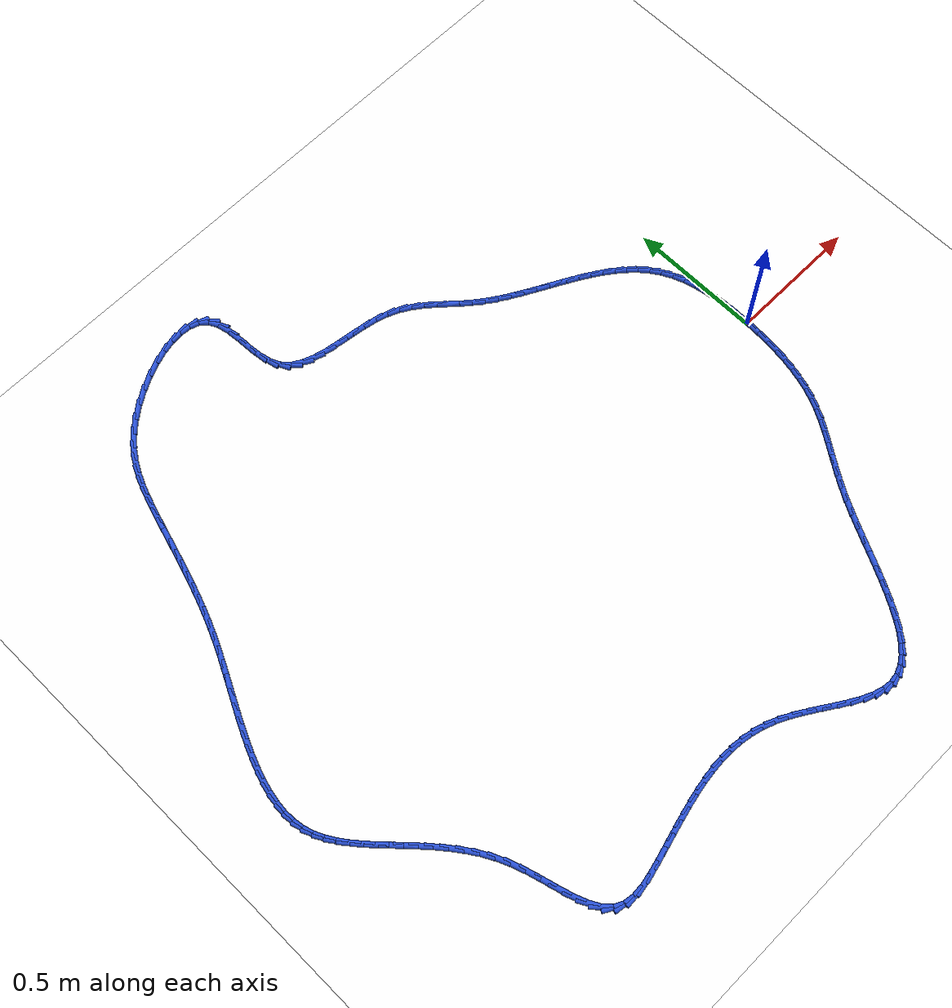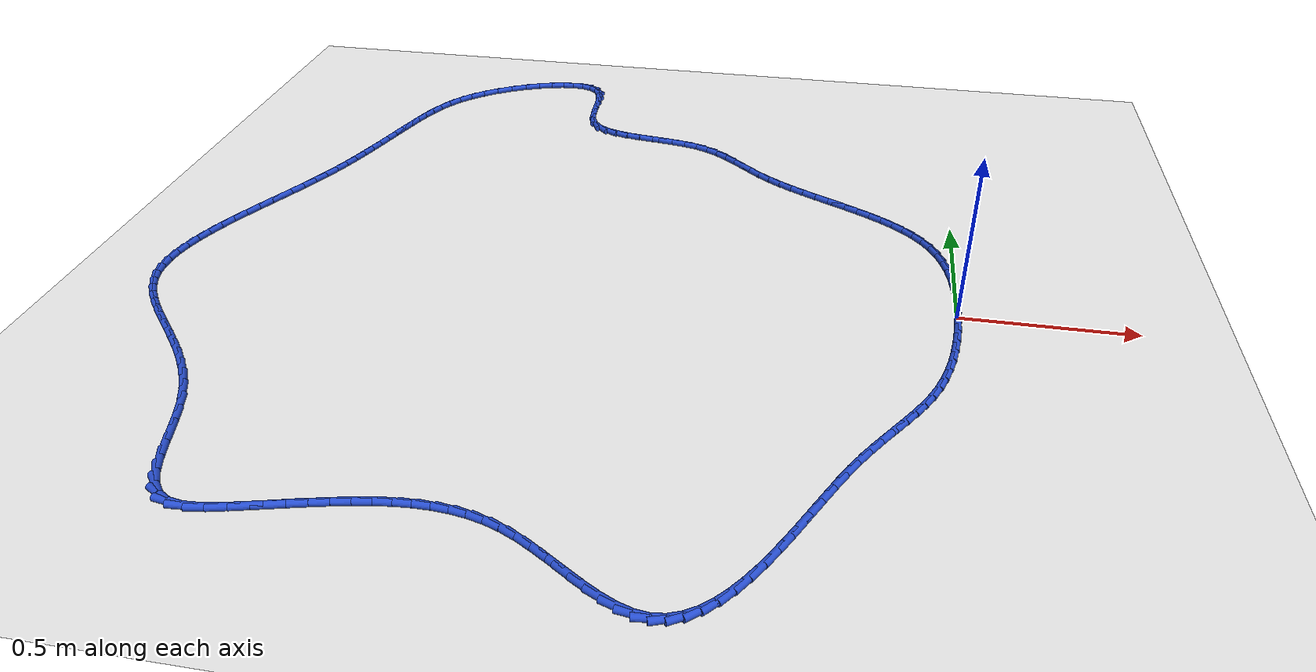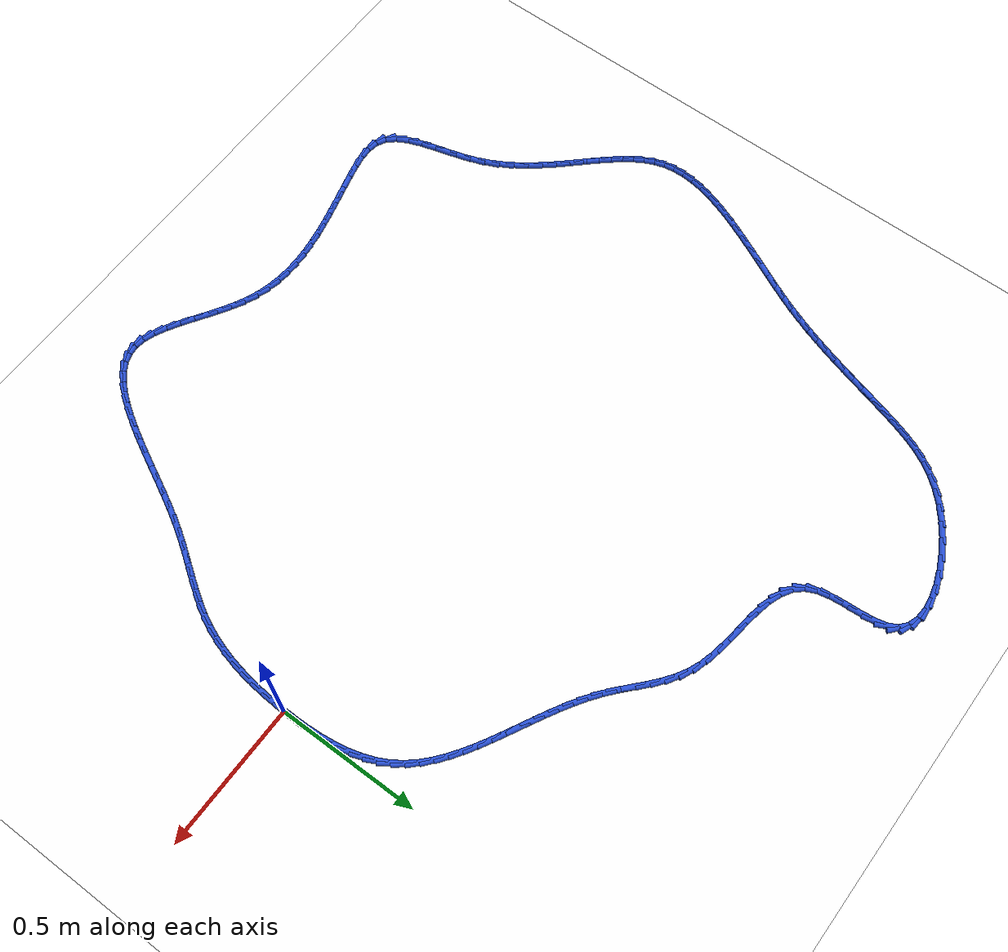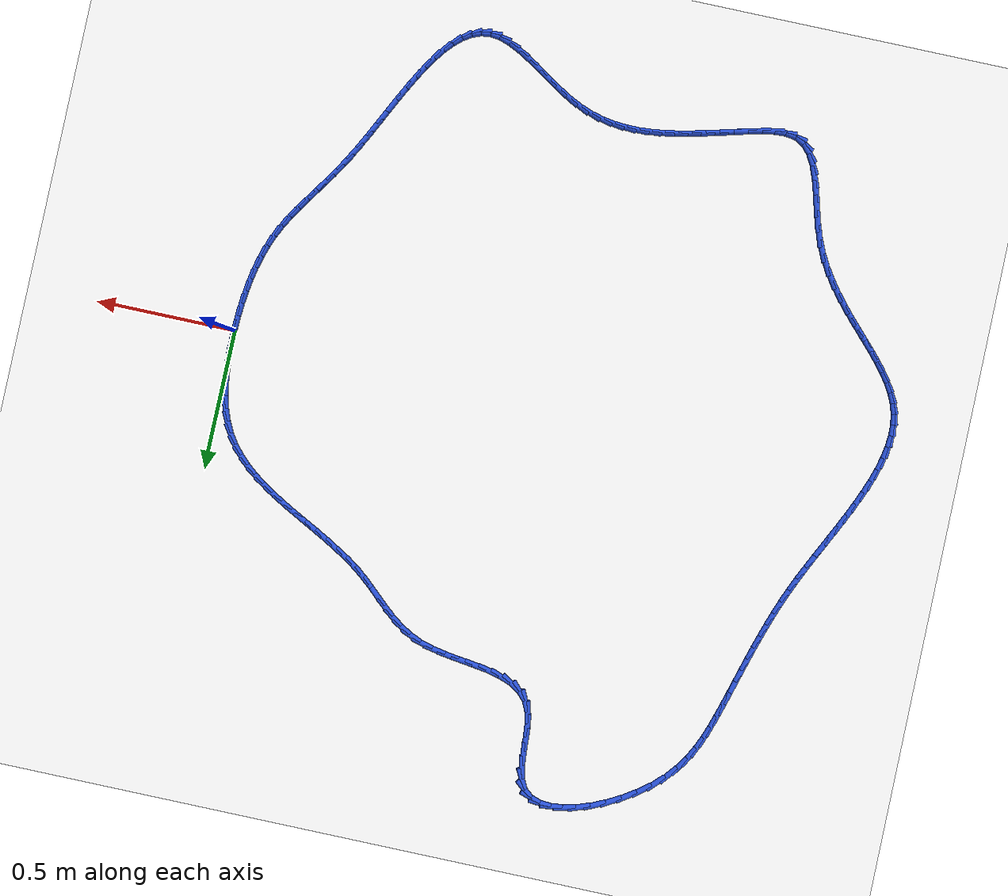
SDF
<sdf version="1.6">
 <world name="default">
  <light name="sun" type="directional">
   <pose>0 0 10 0 -0 0</pose>
   <diffuse>0.8 0.8 0.8 1</diffuse>
   <specular>0.2 0.2 0.2 1</specular>
   <attenuation>
    <range>1000</range>
    <constant>0.9</constant>
    <linear>0.01</linear>
    <quadratic>0.001</quadratic>
   </attenuation>
   <direction>-0.5 0.1 -0.9</direction>
  </light>
  <model name="ground_plane">
   <static>1</static>
   <link name="link">
    <collision name="collision">
     <geometry><plane><normal>0 0 1</normal><size>100 100</size></plane></geometry>
     <surface><friction><ode><mu>100</mu><mu2>50</mu2></ode></friction></surface>
    </collision>
    <visual name="visual">
     <cast_shadows>0</cast_shadows>
     <geometry><plane><normal>0 0 1</normal><size>100 100</size></plane></geometry>
     <material>
      <script><uri>file://media/materials/scripts/gazebo.material</uri><name>Gazebo/WhiteGlow</name></script>
     </material>
    </visual>
   </link>
  </model>
  <gravity>0 0 -9.8</gravity>
  <magnetic_field>6e-06 2.3e-05 -4.2e-05</magnetic_field>
  <atmosphere type="adiabatic"/>
  <physics name="default_physics" default="0" type="ode">
   <max_step_size>0.001</max_step_size>
   <real_time_factor>1</real_time_factor>
   <real_time_update_rate>1000</real_time_update_rate>
  </physics>
  <scene><ambient>0.4 0.4 0.4 1</ambient><background>0.7 0.7 0.7 1</background><shadows>1</shadows></scene>
  <spherical_coordinates>
   <surface_model>EARTH_WGS84</surface_model>
   <latitude_deg>0</latitude_deg>
   <longitude_deg>0</longitude_deg>
   <elevation>0</elevation>
   <heading_deg>0</heading_deg>
  </spherical_coordinates>
  <model name="line">
   <link name="link_0">
    <pose>8.673617379884035e-19 4.163336342344337e-17 0.01 0 1.57 1.5638885327996237</pose>
    <collision name="collision">
     <geometry><cylinder><radius>0.01</radius><length>0.08</length></cylinder></geometry>
    </collision>
    <visual name="visual">
     <material>
      <script><name>Gazebo/Blue</name><uri>file://media/materials/scripts/gazebo.material</uri></script>
     </material>
     <geometry><cylinder><radius>0.01</radius><length>0.08</length></cylinder></geometry>
    </visual>
   </link>
   <link name="link_1">
    <pose>0.00033320009378289483 0.04823461645726469 0.01 0 1.57 -1.542027845524823</pose>
    <collision name="collision">
     <geometry><cylinder><radius>0.01</radius><length>0.08</length></cylinder></geometry>
    </collision>
    <visual name="visual">
     <material>
      <script><name>Gazebo/Blue</name><uri>file://media/materials/scripts/gazebo.material</uri></script>
     </material>
     <geometry><cylinder><radius>0.01</radius><length>0.08</length></cylinder></geometry>
    </visual>
   </link>
   <link name="link_2">
    <pose>-0.0010524073878866967 0.09638541012868167 0.01 0 1.57 -1.4980301199870125</pose>
    <collision name="collision">
     <geometry><cylinder><radius>0.01</radius><length>0.08</length></cylinder></geometry>
    </collision>
    <visual name="visual">
     <material>
      <script><name>Gazebo/Blue</name><uri>file://media/materials/scripts/gazebo.material</uri></script>
     </material>
     <geometry><cylinder><radius>0.01</radius><length>0.08</length></cylinder></geometry>
    </visual>
   </link>
   <link name="link_3">
    <pose>-0.004523898142646754 0.1440086359811894 0.01 0 1.57 -1.4444798290233207</pose>
    <collision name="collision">
     <geometry><cylinder><radius>0.01</radius><length>0.08</length></cylinder></geometry>
    </collision>
    <visual name="visual">
     <material>
      <script><name>Gazebo/Blue</name><uri>file://media/materials/scripts/gazebo.material</uri></script>
     </material>
     <geometry><cylinder><radius>0.01</radius><length>0.08</length></cylinder></geometry>
    </visual>
   </link>
   <link name="link_4">
    <pose>-0.010448347868135255 0.19066054898172638 0.01 0 1.57 -1.3798470282256463</pose>
    <collision name="collision">
     <geometry><cylinder><radius>0.01</radius><length>0.08</length></cylinder></geometry>
    </collision>
    <visual name="visual">
     <material>
      <script><name>Gazebo/Blue</name><uri>file://media/materials/scripts/gazebo.material</uri></script>
     </material>
     <geometry><cylinder><radius>0.01</radius><length>0.08</length></cylinder></geometry>
    </visual>
   </link>
   <link name="link_5">
    <pose>-0.019192832261990186 0.2358974040972311 0.01 0 1.57 -1.3023737410846434</pose>
    <collision name="collision">
     <geometry><cylinder><radius>0.01</radius><length>0.08</length></cylinder></geometry>
    </collision>
    <visual name="visual">
     <material>
      <script><name>Gazebo/Blue</name><uri>file://media/materials/scripts/gazebo.material</uri></script>
     </material>
     <geometry><cylinder><radius>0.01</radius><length>0.08</length></cylinder></geometry>
    </visual>
   </link>
   <link name="link_6">
    <pose>-0.03112442702184952 0.27927545629464184 0.01 0 1.57 -1.2102666559706432</pose>
    <collision name="collision">
     <geometry><cylinder><radius>0.01</radius><length>0.08</length></cylinder></geometry>
    </collision>
    <visual name="visual">
     <material>
      <script><name>Gazebo/Blue</name><uri>file://media/materials/scripts/gazebo.material</uri></script>
     </material>
     <geometry><cylinder><radius>0.01</radius><length>0.08</length></cylinder></geometry>
    </visual>
   </link>
   <link name="link_7">
    <pose>-0.046610207845351234 0.32035096054089734 0.01 0 1.57 -1.1021014326998315</pose>
    <collision name="collision">
     <geometry><cylinder><radius>0.01</radius><length>0.08</length></cylinder></geometry>
    </collision>
    <visual name="visual">
     <material>
      <script><name>Gazebo/Blue</name><uri>file://media/materials/scripts/gazebo.material</uri></script>
     </material>
     <geometry><cylinder><radius>0.01</radius><length>0.08</length></cylinder></geometry>
    </visual>
   </link>
   <link name="link_8">
    <pose>-0.06601725043013332 0.3586801718029359 0.01 0 1.57 -0.9810699827617393</pose>
    <collision name="collision">
     <geometry><cylinder><radius>0.01</radius><length>0.08</length></cylinder></geometry>
    </collision>
    <visual name="visual">
     <material>
      <script><name>Gazebo/Blue</name><uri>file://media/materials/scripts/gazebo.material</uri></script>
     </material>
     <geometry><cylinder><radius>0.01</radius><length>0.08</length></cylinder></geometry>
    </visual>
   </link>
   <link name="link_9">
    <pose>-0.08960336815751724 0.39392755590297973 0.01 0 1.57 -0.8667612638911113</pose>
    <collision name="collision">
     <geometry><cylinder><radius>0.01</radius><length>0.08</length></cylinder></geometry>
    </collision>
    <visual name="visual">
     <material>
      <script><name>Gazebo/Blue</name><uri>file://media/materials/scripts/gazebo.material</uri></script>
     </material>
     <geometry><cylinder><radius>0.01</radius><length>0.08</length></cylinder></geometry>
    </visual>
   </link>
   <link name="link_10">
    <pose>-0.11708719861495066 0.4262915658215913 0.01 0 1.57 -0.7674553291350986</pose>
    <collision name="collision">
     <geometry><cylinder><radius>0.01</radius><length>0.08</length></cylinder></geometry>
    </collision>
    <visual name="visual">
     <material>
      <script><name>Gazebo/Blue</name><uri>file://media/materials/scripts/gazebo.material</uri></script>
     </material>
     <geometry><cylinder><radius>0.01</radius><length>0.08</length></cylinder></geometry>
    </visual>
   </link>
   <link name="link_11">
    <pose>-0.1480213548800331 0.4561350813500975 0.01 0 1.57 -0.6843029180578902</pose>
    <collision name="collision">
     <geometry><cylinder><radius>0.01</radius><length>0.08</length></cylinder></geometry>
    </collision>
    <visual name="visual">
     <material>
      <script><name>Gazebo/Blue</name><uri>file://media/materials/scripts/gazebo.material</uri></script>
     </material>
     <geometry><cylinder><radius>0.01</radius><length>0.08</length></cylinder></geometry>
    </visual>
   </link>
   <link name="link_12">
    <pose>-0.1819584038611522 0.4838210280047396 0.01 0 1.57 -0.6170709906054938</pose>
    <collision name="collision">
     <geometry><cylinder><radius>0.01</radius><length>0.08</length></cylinder></geometry>
    </collision>
    <visual name="visual">
     <material>
      <script><name>Gazebo/Blue</name><uri>file://media/materials/scripts/gazebo.material</uri></script>
     </material>
     <geometry><cylinder><radius>0.01</radius><length>0.08</length></cylinder></geometry>
    </visual>
   </link>
   <link name="link_13">
    <pose>-0.21845091246669512 0.5097123313017579 0.01 0 1.57 -0.5648019596562728</pose>
    <collision name="collision">
     <geometry><cylinder><radius>0.01</radius><length>0.08</length></cylinder></geometry>
    </collision>
    <visual name="visual">
     <material>
      <script><name>Gazebo/Blue</name><uri>file://media/materials/scripts/gazebo.material</uri></script>
     </material>
     <geometry><cylinder><radius>0.01</radius><length>0.08</length></cylinder></geometry>
    </visual>
   </link>
   <link name="link_14">
    <pose>-0.2570514476050492 0.5341719167573932 0.01 0 1.57 -0.5263146158345897</pose>
    <collision name="collision">
     <geometry><cylinder><radius>0.01</radius><length>0.08</length></cylinder></geometry>
    </collision>
    <visual name="visual">
     <material>
      <script><name>Gazebo/Blue</name><uri>file://media/materials/scripts/gazebo.material</uri></script>
     </material>
     <geometry><cylinder><radius>0.01</radius><length>0.08</length></cylinder></geometry>
    </visual>
   </link>
   <link name="link_15">
    <pose>-0.29731257618460194 0.5575627098878863 0.01 0 1.57 -0.5005090120355066</pose>
    <collision name="collision">
     <geometry><cylinder><radius>0.01</radius><length>0.08</length></cylinder></geometry>
    </collision>
    <visual name="visual">
     <material>
      <script><name>Gazebo/Blue</name><uri>file://media/materials/scripts/gazebo.material</uri></script>
     </material>
     <geometry><cylinder><radius>0.01</radius><length>0.08</length></cylinder></geometry>
    </visual>
   </link>
   <link name="link_16">
    <pose>-0.3387868651137407 0.5802476362094778 0.01 0 1.57 -0.48652236502355717</pose>
    <collision name="collision">
     <geometry><cylinder><radius>0.01</radius><length>0.08</length></cylinder></geometry>
    </collision>
    <visual name="visual">
     <material>
      <script><name>Gazebo/Blue</name><uri>file://media/materials/scripts/gazebo.material</uri></script>
     </material>
     <geometry><cylinder><radius>0.01</radius><length>0.08</length></cylinder></geometry>
    </visual>
   </link>
   <link name="link_17">
    <pose>-0.38102688130085255 0.6025896212384084 0.01 0 1.57 -0.4837942739647934</pose>
    <collision name="collision">
     <geometry><cylinder><radius>0.01</radius><length>0.08</length></cylinder></geometry>
    </collision>
    <visual name="visual">
     <material>
      <script><name>Gazebo/Blue</name><uri>file://media/materials/scripts/gazebo.material</uri></script>
     </material>
     <geometry><cylinder><radius>0.01</radius><length>0.08</length></cylinder></geometry>
    </visual>
   </link>
   <link name="link_18">
    <pose>-0.42358519165432507 0.6249515904909191 0.01 0 1.57 -0.49208320364753905</pose>
    <collision name="collision">
     <geometry><cylinder><radius>0.01</radius><length>0.08</length></cylinder></geometry>
    </collision>
    <visual name="visual">
     <material>
      <script><name>Gazebo/Blue</name><uri>file://media/materials/scripts/gazebo.material</uri></script>
     </material>
     <geometry><cylinder><radius>0.01</radius><length>0.08</length></cylinder></geometry>
    </visual>
   </link>
   <link name="link_19">
    <pose>-0.4660143630825456 0.6476964694832503 0.01 0 1.57 -0.5114565291394675</pose>
    <collision name="collision">
     <geometry><cylinder><radius>0.01</radius><length>0.08</length></cylinder></geometry>
    </collision>
    <visual name="visual">
     <material>
      <script><name>Gazebo/Blue</name><uri>file://media/materials/scripts/gazebo.material</uri></script>
     </material>
     <geometry><cylinder><radius>0.01</radius><length>0.08</length></cylinder></geometry>
    </visual>
   </link>
   <link name="link_20">
    <pose>-0.5078669624939016 0.671187183731643 0.01 0 1.57 -0.5422601459008642</pose>
    <collision name="collision">
     <geometry><cylinder><radius>0.01</radius><length>0.08</length></cylinder></geometry>
    </collision>
    <visual name="visual">
     <material>
      <script><name>Gazebo/Blue</name><uri>file://media/materials/scripts/gazebo.material</uri></script>
     </material>
     <geometry><cylinder><radius>0.01</radius><length>0.08</length></cylinder></geometry>
    </visual>
   </link>
   <link name="link_21">
    <pose>-0.5486955567967804 0.6957866587523376 0.01 0 1.57 -0.5850602636240366</pose>
    <collision name="collision">
     <geometry><cylinder><radius>0.01</radius><length>0.08</length></cylinder></geometry>
    </collision>
    <visual name="visual">
     <material>
      <script><name>Gazebo/Blue</name><uri>file://media/materials/scripts/gazebo.material</uri></script>
     </material>
     <geometry><cylinder><radius>0.01</radius><length>0.08</length></cylinder></geometry>
    </visual>
   </link>
   <link name="link_22">
    <pose>-0.588052712899569 0.7218578200615751 0.01 0 1.57 -0.6405381645431764</pose>
    <collision name="collision">
     <geometry><cylinder><radius>0.01</radius><length>0.08</length></cylinder></geometry>
    </collision>
    <visual name="visual">
     <material>
      <script><name>Gazebo/Blue</name><uri>file://media/materials/scripts/gazebo.material</uri></script>
     </material>
     <geometry><cylinder><radius>0.01</radius><length>0.08</length></cylinder></geometry>
    </visual>
   </link>
   <link name="link_23">
    <pose>-0.6254909977106555 0.7497635931755963 0.01 0 1.57 -0.701884966377041</pose>
    <collision name="collision">
     <geometry><cylinder><radius>0.01</radius><length>0.08</length></cylinder></geometry>
    </collision>
    <visual name="visual">
     <material>
      <script><name>Gazebo/Blue</name><uri>file://media/materials/scripts/gazebo.material</uri></script>
     </material>
     <geometry><cylinder><radius>0.01</radius><length>0.08</length></cylinder></geometry>
    </visual>
   </link>
   <link name="link_24">
    <pose>-0.6608030714660044 0.7796205081808602 0.01 0 1.57 -0.7374043222740496</pose>
    <collision name="collision">
     <geometry><cylinder><radius>0.01</radius><length>0.08</length></cylinder></geometry>
    </collision>
    <visual name="visual">
     <material>
      <script><name>Gazebo/Blue</name><uri>file://media/materials/scripts/gazebo.material</uri></script>
     </material>
     <geometry><cylinder><radius>0.01</radius><length>0.08</length></cylinder></geometry>
    </visual>
   </link>
   <link name="link_25">
    <pose>-0.6947992999565886 0.8105006763115948 0.01 0 1.57 -0.7379386256422358</pose>
    <collision name="collision">
     <geometry><cylinder><radius>0.01</radius><length>0.08</length></cylinder></geometry>
    </collision>
    <visual name="visual">
     <material>
      <script><name>Gazebo/Blue</name><uri>file://media/materials/scripts/gazebo.material</uri></script>
     </material>
     <geometry><cylinder><radius>0.01</radius><length>0.08</length></cylinder></geometry>
    </visual>
   </link>
   <link name="link_26">
    <pose>-0.7285596538375517 0.8411995272005497 0.01 0 1.57 -0.7028001510497276</pose>
    <collision name="collision">
     <geometry><cylinder><radius>0.01</radius><length>0.08</length></cylinder></geometry>
    </collision>
    <visual name="visual">
     <material>
      <script><name>Gazebo/Blue</name><uri>file://media/materials/scripts/gazebo.material</uri></script>
     </material>
     <geometry><cylinder><radius>0.01</radius><length>0.08</length></cylinder></geometry>
    </visual>
   </link>
   <link name="link_27">
    <pose>-0.7631641056009044 0.8705124885953921 0.01 0 1.57 -0.6315892234551607</pose>
    <collision name="collision">
     <geometry><cylinder><radius>0.01</radius><length>0.08</length></cylinder></geometry>
    </collision>
    <visual name="visual">
     <material>
      <script><name>Gazebo/Blue</name><uri>file://media/materials/scripts/gazebo.material</uri></script>
     </material>
     <geometry><cylinder><radius>0.01</radius><length>0.08</length></cylinder></geometry>
    </visual>
   </link>
   <link name="link_28">
    <pose>-0.7996926277386576 0.8972349882437898 0.01 0 1.57 -0.5255568762798322</pose>
    <collision name="collision">
     <geometry><cylinder><radius>0.01</radius><length>0.08</length></cylinder></geometry>
    </collision>
    <visual name="visual">
     <material>
      <script><name>Gazebo/Blue</name><uri>file://media/materials/scripts/gazebo.material</uri></script>
     </material>
     <geometry><cylinder><radius>0.01</radius><length>0.08</length></cylinder></geometry>
    </visual>
   </link>
   <link name="link_29">
    <pose>-0.8392251927428213 0.9201624538934101 0.01 0 1.57 -0.39076782244642055</pose>
    <collision name="collision">
     <geometry><cylinder><radius>0.01</radius><length>0.08</length></cylinder></geometry>
    </collision>
    <visual name="visual">
     <material>
      <script><name>Gazebo/Blue</name><uri>file://media/materials/scripts/gazebo.material</uri></script>
     </material>
     <geometry><cylinder><radius>0.01</radius><length>0.08</length></cylinder></geometry>
    </visual>
   </link>
   <link name="link_30">
    <pose>-0.8828147587954682 0.9381192958116363 0.01 0 1.57 -0.2655494144139299</pose>
    <collision name="collision">
     <geometry><cylinder><radius>0.01</radius><length>0.08</length></cylinder></geometry>
    </collision>
    <visual name="visual">
     <material>
      <script><name>Gazebo/Blue</name><uri>file://media/materials/scripts/gazebo.material</uri></script>
     </material>
     <geometry><cylinder><radius>0.01</radius><length>0.08</length></cylinder></geometry>
    </visual>
   </link>
   <link name="link_31">
    <pose>-0.9304477525631661 0.9510741611812925 0.01 0 1.57 -0.18521239035500037</pose>
    <collision name="collision">
     <geometry><cylinder><radius>0.01</radius><length>0.08</length></cylinder></geometry>
    </collision>
    <visual name="visual">
     <material>
      <script><name>Gazebo/Blue</name><uri>file://media/materials/scripts/gazebo.material</uri></script>
     </material>
     <geometry><cylinder><radius>0.01</radius><length>0.08</length></cylinder></geometry>
    </visual>
   </link>
   <link name="link_32">
    <pose>-0.9807156047786213 0.9604923297939961 0.01 0 1.57 -0.14389766916247382</pose>
    <collision name="collision">
     <geometry><cylinder><radius>0.01</radius><length>0.08</length></cylinder></geometry>
    </collision>
    <visual name="visual">
     <material>
      <script><name>Gazebo/Blue</name><uri>file://media/materials/scripts/gazebo.material</uri></script>
     </material>
     <geometry><cylinder><radius>0.01</radius><length>0.08</length></cylinder></geometry>
    </visual>
   </link>
   <link name="link_33">
    <pose>-1.0321155510144813 0.9679401394765276 0.01 0 1.57 -0.1371674760556057</pose>
    <collision name="collision">
     <geometry><cylinder><radius>0.01</radius><length>0.08</length></cylinder></geometry>
    </collision>
    <visual name="visual">
     <material>
      <script><name>Gazebo/Blue</name><uri>file://media/materials/scripts/gazebo.material</uri></script>
     </material>
     <geometry><cylinder><radius>0.01</radius><length>0.08</length></cylinder></geometry>
    </visual>
   </link>
   <link name="link_34">
    <pose>-1.0831448268433932 0.9749839280556668 0.01 0 1.57 -0.16541518962619706</pose>
    <collision name="collision">
     <geometry><cylinder><radius>0.01</radius><length>0.08</length></cylinder></geometry>
    </collision>
    <visual name="visual">
     <material>
      <script><name>Gazebo/Blue</name><uri>file://media/materials/scripts/gazebo.material</uri></script>
     </material>
     <geometry><cylinder><radius>0.01</radius><length>0.08</length></cylinder></geometry>
    </visual>
   </link>
   <link name="link_35">
    <pose>-1.1323006678380052 0.9831900333581948 0.01 0 1.57 -0.2344633725893443</pose>
    <collision name="collision">
     <geometry><cylinder><radius>0.01</radius><length>0.08</length></cylinder></geometry>
    </collision>
    <visual name="visual">
     <material>
      <script><name>Gazebo/Blue</name><uri>file://media/materials/scripts/gazebo.material</uri></script>
     </material>
     <geometry><cylinder><radius>0.01</radius><length>0.08</length></cylinder></geometry>
    </visual>
   </link>
   <link name="link_36">
    <pose>-1.1780803095709633 0.9941247932108909 0.01 0 1.57 -0.3564536226096373</pose>
    <collision name="collision">
     <geometry><cylinder><radius>0.01</radius><length>0.08</length></cylinder></geometry>
    </collision>
    <visual name="visual">
     <material>
      <script><name>Gazebo/Blue</name><uri>file://media/materials/scripts/gazebo.material</uri></script>
     </material>
     <geometry><cylinder><radius>0.01</radius><length>0.08</length></cylinder></geometry>
    </visual>
   </link>
   <link name="link_37">
    <pose>-1.2189809876149162 1.009354545440536 0.01 0 1.57 -0.5484685845353197</pose>
    <collision name="collision">
     <geometry><cylinder><radius>0.01</radius><length>0.08</length></cylinder></geometry>
    </collision>
    <visual name="visual">
     <material>
      <script><name>Gazebo/Blue</name><uri>file://media/materials/scripts/gazebo.material</uri></script>
     </material>
     <geometry><cylinder><radius>0.01</radius><length>0.08</length></cylinder></geometry>
    </visual>
   </link>
   <link name="link_38">
    <pose>-1.25349993754251 1.0304456278739094 0.01 0 1.57 -0.8195495851167237</pose>
    <collision name="collision">
     <geometry><cylinder><radius>0.01</radius><length>0.08</length></cylinder></geometry>
    </collision>
    <visual name="visual">
     <material>
      <script><name>Gazebo/Blue</name><uri>file://media/materials/scripts/gazebo.material</uri></script>
     </material>
     <geometry><cylinder><radius>0.01</radius><length>0.08</length></cylinder></geometry>
    </visual>
   </link>
   <link name="link_39">
    <pose>-1.280134394926393 1.0589643783377927 0.01 0 1.57 -1.1343944330731641</pose>
    <collision name="collision">
     <geometry><cylinder><radius>0.01</radius><length>0.08</length></cylinder></geometry>
    </collision>
    <visual name="visual">
     <material>
      <script><name>Gazebo/Blue</name><uri>file://media/materials/scripts/gazebo.material</uri></script>
     </material>
     <geometry><cylinder><radius>0.01</radius><length>0.08</length></cylinder></geometry>
    </visual>
   </link>
   <link name="link_40">
    <pose>-1.2975490972540165 1.096303544656579 0.01 0 1.57 -1.3648231087718672</pose>
    <collision name="collision">
     <geometry><cylinder><radius>0.01</radius><length>0.08</length></cylinder></geometry>
    </collision>
    <visual name="visual">
     <material>
      <script><name>Gazebo/Blue</name><uri>file://media/materials/scripts/gazebo.material</uri></script>
     </material>
     <geometry><cylinder><radius>0.01</radius><length>0.08</length></cylinder></geometry>
    </visual>
   </link>
   <link name="link_41">
    <pose>-1.3069370573626427 1.1412357056582705 0.01 0 1.57 -1.4794764498383255</pose>
    <collision name="collision">
     <geometry><cylinder><radius>0.01</radius><length>0.08</length></cylinder></geometry>
    </collision>
    <visual name="visual">
     <material>
      <script><name>Gazebo/Blue</name><uri>file://media/materials/scripts/gazebo.material</uri></script>
     </material>
     <geometry><cylinder><radius>0.01</radius><length>0.08</length></cylinder></geometry>
    </visual>
   </link>
   <link name="link_42">
    <pose>-1.311448847396816 1.1905047306768972 0.01 0 1.57 -1.5144469195663282</pose>
    <collision name="collision">
     <geometry><cylinder><radius>0.01</radius><length>0.08</length></cylinder></geometry>
    </collision>
    <visual name="visual">
     <material>
      <script><name>Gazebo/Blue</name><uri>file://media/materials/scripts/gazebo.material</uri></script>
     </material>
     <geometry><cylinder><radius>0.01</radius><length>0.08</length></cylinder></geometry>
    </visual>
   </link>
   <link name="link_43">
    <pose>-1.314286051071564 1.240801623390283 0.01 0 1.57 -1.480154377767913</pose>
    <collision name="collision">
     <geometry><cylinder><radius>0.01</radius><length>0.08</length></cylinder></geometry>
    </collision>
    <visual name="visual">
     <material>
      <script><name>Gazebo/Blue</name><uri>file://media/materials/scripts/gazebo.material</uri></script>
     </material>
     <geometry><cylinder><radius>0.01</radius><length>0.08</length></cylinder></geometry>
    </visual>
   </link>
   <link name="link_44">
    <pose>-1.3186502521019146 1.2888173874762514 0.01 0 1.57 -1.359667528855535</pose>
    <collision name="collision">
     <geometry><cylinder><radius>0.01</radius><length>0.08</length></cylinder></geometry>
    </collision>
    <visual name="visual">
     <material>
      <script><name>Gazebo/Blue</name><uri>file://media/materials/scripts/gazebo.material</uri></script>
     </material>
     <geometry><cylinder><radius>0.01</radius><length>0.08</length></cylinder></geometry>
    </visual>
   </link>
   <link name="link_45">
    <pose>-1.3277430342028946 1.3312430266126254 0.01 0 1.57 -1.1013886630562095</pose>
    <collision name="collision">
     <geometry><cylinder><radius>0.01</radius><length>0.08</length></cylinder></geometry>
    </collision>
    <visual name="visual">
     <material>
      <script><name>Gazebo/Blue</name><uri>file://media/materials/scripts/gazebo.material</uri></script>
     </material>
     <geometry><cylinder><radius>0.01</radius><length>0.08</length></cylinder></geometry>
    </visual>
   </link>
   <link name="link_46">
    <pose>-1.3447538314881593 1.3647802798740278 0.01 0 1.57 -0.7059317822519278</pose>
    <collision name="collision">
     <geometry><cylinder><radius>0.01</radius><length>0.08</length></cylinder></geometry>
    </collision>
    <visual name="visual">
     <material>
      <script><name>Gazebo/Blue</name><uri>file://media/materials/scripts/gazebo.material</uri></script>
     </material>
     <geometry><cylinder><radius>0.01</radius><length>0.08</length></cylinder></geometry>
    </visual>
   </link>
   <link name="link_47">
    <pose>-1.3713631487655171 1.3874641773907088 0.01 0 1.57 -0.34293012655371324</pose>
    <collision name="collision">
     <geometry><cylinder><radius>0.01</radius><length>0.08</length></cylinder></geometry>
    </collision>
    <visual name="visual">
     <material>
      <script><name>Gazebo/Blue</name><uri>file://media/materials/scripts/gazebo.material</uri></script>
     </material>
     <geometry><cylinder><radius>0.01</radius><length>0.08</length></cylinder></geometry>
    </visual>
   </link>
   <link name="link_48">
    <pose>-1.4062998065734147 1.3999378597061307 0.01 0 1.57 -0.07689080052161715</pose>
    <collision name="collision">
     <geometry><cylinder><radius>0.01</radius><length>0.08</length></cylinder></geometry>
    </collision>
    <visual name="visual">
     <material>
      <script><name>Gazebo/Blue</name><uri>file://media/materials/scripts/gazebo.material</uri></script>
     </material>
     <geometry><cylinder><radius>0.01</radius><length>0.08</length></cylinder></geometry>
    </visual>
   </link>
   <link name="link_49">
    <pose>-1.447950529627325 1.4031467434870772 0.01 0 1.57 0.10887963148186547</pose>
    <collision name="collision">
     <geometry><cylinder><radius>0.01</radius><length>0.08</length></cylinder></geometry>
    </collision>
    <visual name="visual">
     <material>
      <script><name>Gazebo/Blue</name><uri>file://media/materials/scripts/gazebo.material</uri></script>
     </material>
     <geometry><cylinder><radius>0.01</radius><length>0.08</length></cylinder></geometry>
    </visual>
   </link>
   <link name="link_50">
    <pose>-1.4947020426427213 1.398036245400332 0.01 0 1.57 0.2435676177190749</pose>
    <collision name="collision">
     <geometry><cylinder><radius>0.01</radius><length>0.08</length></cylinder></geometry>
    </collision>
    <visual name="visual">
     <material>
      <script><name>Gazebo/Blue</name><uri>file://media/materials/scripts/gazebo.material</uri></script>
     </material>
     <geometry><cylinder><radius>0.01</radius><length>0.08</length></cylinder></geometry>
    </visual>
   </link>
   <link name="link_51">
    <pose>-1.5449410703350772 1.3855517821126788 0.01 0 1.57 0.34813925829511083</pose>
    <collision name="collision">
     <geometry><cylinder><radius>0.01</radius><length>0.08</length></cylinder></geometry>
    </collision>
    <visual name="visual">
     <material>
      <script><name>Gazebo/Blue</name><uri>file://media/materials/scripts/gazebo.material</uri></script>
     </material>
     <geometry><cylinder><radius>0.01</radius><length>0.08</length></cylinder></geometry>
    </visual>
   </link>
   <link name="link_52">
    <pose>-1.5970543374198667 1.3666387702909015 0.01 0 1.57 0.435918802975157</pose>
    <collision name="collision">
     <geometry><cylinder><radius>0.01</radius><length>0.08</length></cylinder></geometry>
    </collision>
    <visual name="visual">
     <material>
      <script><name>Gazebo/Blue</name><uri>file://media/materials/scripts/gazebo.material</uri></script>
     </material>
     <geometry><cylinder><radius>0.01</radius><length>0.08</length></cylinder></geometry>
    </visual>
   </link>
   <link name="link_53">
    <pose>-1.649428568612562 1.342242626601784 0.01 0 1.57 0.5158669880957145</pose>
    <collision name="collision">
     <geometry><cylinder><radius>0.01</radius><length>0.08</length></cylinder></geometry>
    </collision>
    <visual name="visual">
     <material>
      <script><name>Gazebo/Blue</name><uri>file://media/materials/scripts/gazebo.material</uri></script>
     </material>
     <geometry><cylinder><radius>0.01</radius><length>0.08</length></cylinder></geometry>
    </visual>
   </link>
   <link name="link_54">
    <pose>-1.7004504886286371 1.31330876771211 0.01 0 1.57 0.5950084919057425</pose>
    <collision name="collision">
     <geometry><cylinder><radius>0.01</radius><length>0.08</length></cylinder></geometry>
    </collision>
    <visual name="visual">
     <material>
      <script><name>Gazebo/Blue</name><uri>file://media/materials/scripts/gazebo.material</uri></script>
     </material>
     <geometry><cylinder><radius>0.01</radius><length>0.08</length></cylinder></geometry>
    </visual>
   </link>
   <link name="link_55">
    <pose>-1.748506822183566 1.2807826102886628 0.01 0 1.57 0.6802014326812069</pose>
    <collision name="collision">
     <geometry><cylinder><radius>0.01</radius><length>0.08</length></cylinder></geometry>
    </collision>
    <visual name="visual">
     <material>
      <script><name>Gazebo/Blue</name><uri>file://media/materials/scripts/gazebo.material</uri></script>
     </material>
     <geometry><cylinder><radius>0.01</radius><length>0.08</length></cylinder></geometry>
    </visual>
   </link>
   <link name="link_56">
    <pose>-1.7919842939928206 1.2456095709982264 0.01 0 1.57 0.7790559082850623</pose>
    <collision name="collision">
     <geometry><cylinder><radius>0.01</radius><length>0.08</length></cylinder></geometry>
    </collision>
    <visual name="visual">
     <material>
      <script><name>Gazebo/Blue</name><uri>file://media/materials/scripts/gazebo.material</uri></script>
     </material>
     <geometry><cylinder><radius>0.01</radius><length>0.08</length></cylinder></geometry>
    </visual>
   </link>
   <link name="link_57">
    <pose>-1.8293564521310786 1.2087084790759823 0.01 0 1.57 0.8866111480364854</pose>
    <collision name="collision">
     <geometry><cylinder><radius>0.01</radius><length>0.08</length></cylinder></geometry>
    </collision>
    <visual name="visual">
     <material>
      <script><name>Gazebo/Blue</name><uri>file://media/materials/scripts/gazebo.material</uri></script>
     </material>
     <geometry><cylinder><radius>0.01</radius><length>0.08</length></cylinder></geometry>
    </visual>
   </link>
   <link name="link_58">
    <pose>-1.8604516114212468 1.1705833011142934 0.01 0 1.57 0.9898453960514884</pose>
    <collision name="collision">
     <geometry><cylinder><radius>0.01</radius><length>0.08</length></cylinder></geometry>
    </collision>
    <visual name="visual">
     <material>
      <script><name>Gazebo/Blue</name><uri>file://media/materials/scripts/gazebo.material</uri></script>
     </material>
     <geometry><cylinder><radius>0.01</radius><length>0.08</length></cylinder></geometry>
    </visual>
   </link>
   <link name="link_59">
    <pose>-1.8861701947621046 1.1314096980467707 0.01 0 1.57 1.082611386101768</pose>
    <collision name="collision">
     <geometry><cylinder><radius>0.01</radius><length>0.08</length></cylinder></geometry>
    </collision>
    <visual name="visual">
     <material>
      <script><name>Gazebo/Blue</name><uri>file://media/materials/scripts/gazebo.material</uri></script>
     </material>
     <geometry><cylinder><radius>0.01</radius><length>0.08</length></cylinder></geometry>
    </visual>
   </link>
   <link name="link_60">
    <pose>-1.9074419445305126 1.0913543524672606 0.01 0 1.57 1.1600833930629615</pose>
    <collision name="collision">
     <geometry><cylinder><radius>0.01</radius><length>0.08</length></cylinder></geometry>
    </collision>
    <visual name="visual">
     <material>
      <script><name>Gazebo/Blue</name><uri>file://media/materials/scripts/gazebo.material</uri></script>
     </material>
     <geometry><cylinder><radius>0.01</radius><length>0.08</length></cylinder></geometry>
    </visual>
   </link>
   <link name="link_61">
    <pose>-1.9251966031033325 1.0505839469696105 0.01 0 1.57 1.21898699913098</pose>
    <collision name="collision">
     <geometry><cylinder><radius>0.01</radius><length>0.08</length></cylinder></geometry>
    </collision>
    <visual name="visual">
     <material>
      <script><name>Gazebo/Blue</name><uri>file://media/materials/scripts/gazebo.material</uri></script>
     </material>
     <geometry><cylinder><radius>0.01</radius><length>0.08</length></cylinder></geometry>
    </visual>
   </link>
   <link name="link_62">
    <pose>-1.9403639128574246 1.009265164147668 0.01 0 1.57 1.257496318050746</pose>
    <collision name="collision">
     <geometry><cylinder><radius>0.01</radius><length>0.08</length></cylinder></geometry>
    </collision>
    <visual name="visual">
     <material>
      <script><name>Gazebo/Blue</name><uri>file://media/materials/scripts/gazebo.material</uri></script>
     </material>
     <geometry><cylinder><radius>0.01</radius><length>0.08</length></cylinder></geometry>
    </visual>
   </link>
   <link name="link_63">
    <pose>-1.9538736161696502 0.9675646865952794 0.01 0 1.57 1.2760436209046493</pose>
    <collision name="collision">
     <geometry><cylinder><radius>0.01</radius><length>0.08</length></cylinder></geometry>
    </collision>
    <visual name="visual">
     <material>
      <script><name>Gazebo/Blue</name><uri>file://media/materials/scripts/gazebo.material</uri></script>
     </material>
     <geometry><cylinder><radius>0.01</radius><length>0.08</length></cylinder></geometry>
    </visual>
   </link>
   <link name="link_64">
    <pose>-1.966603048253803 0.9256358489963472 0.01 0 1.57 1.2850031332400407</pose>
    <collision name="collision">
     <geometry><cylinder><radius>0.01</radius><length>0.08</length></cylinder></geometry>
    </collision>
    <visual name="visual">
     <material>
      <script><name>Gazebo/Blue</name><uri>file://media/materials/scripts/gazebo.material</uri></script>
     </material>
     <geometry><cylinder><radius>0.01</radius><length>0.08</length></cylinder></geometry>
    </visual>
   </link>
   <link name="link_65">
    <pose>-1.9789790549800668 0.8835172480707604 0.01 0 1.57 1.2897454069455458</pose>
    <collision name="collision">
     <geometry><cylinder><radius>0.01</radius><length>0.08</length></cylinder></geometry>
    </collision>
    <visual name="visual">
     <material>
      <script><name>Gazebo/Blue</name><uri>file://media/materials/scripts/gazebo.material</uri></script>
     </material>
     <geometry><cylinder><radius>0.01</radius><length>0.08</length></cylinder></geometry>
    </visual>
   </link>
   <link name="link_66">
    <pose>-1.9911989002426242 0.8411890068611181 0.01 0 1.57 1.2903337179077154</pose>
    <collision name="collision">
     <geometry><cylinder><radius>0.01</radius><length>0.08</length></cylinder></geometry>
    </collision>
    <visual name="visual">
     <material>
      <script><name>Gazebo/Blue</name><uri>file://media/materials/scripts/gazebo.material</uri></script>
     </material>
     <geometry><cylinder><radius>0.01</radius><length>0.08</length></cylinder></geometry>
    </visual>
   </link>
   <link name="link_67">
    <pose>-2.0034580202247465 0.7986307828988353 0.01 0 1.57 1.2868299119979763</pose>
    <collision name="collision">
     <geometry><cylinder><radius>0.01</radius><length>0.08</length></cylinder></geometry>
    </collision>
    <visual name="visual">
     <material>
      <script><name>Gazebo/Blue</name><uri>file://media/materials/scripts/gazebo.material</uri></script>
     </material>
     <geometry><cylinder><radius>0.01</radius><length>0.08</length></cylinder></geometry>
    </visual>
   </link>
   <link name="link_68">
    <pose>-2.0159518511097048 0.7558222337153248 0.01 0 1.57 1.2793349981316864</pose>
    <collision name="collision">
     <geometry><cylinder><radius>0.01</radius><length>0.08</length></cylinder></geometry>
    </collision>
    <visual name="visual">
     <material>
      <script><name>Gazebo/Blue</name><uri>file://media/materials/scripts/gazebo.material</uri></script>
     </material>
     <geometry><cylinder><radius>0.01</radius><length>0.08</length></cylinder></geometry>
    </visual>
   </link>
   <link name="link_69">
    <pose>-2.028875829080769 0.7127430168420008 0.01 0 1.57 1.2679878106480476</pose>
    <collision name="collision">
     <geometry><cylinder><radius>0.01</radius><length>0.08</length></cylinder></geometry>
    </collision>
    <visual name="visual">
     <material>
      <script><name>Gazebo/Blue</name><uri>file://media/materials/scripts/gazebo.material</uri></script>
     </material>
     <geometry><cylinder><radius>0.01</radius><length>0.08</length></cylinder></geometry>
    </visual>
   </link>
   <link name="link_70">
    <pose>-2.0424253903212106 0.6693727898102769 0.01 0 1.57 1.2529644424801447</pose>
    <collision name="collision">
     <geometry><cylinder><radius>0.01</radius><length>0.08</length></cylinder></geometry>
    </collision>
    <visual name="visual">
     <material>
      <script><name>Gazebo/Blue</name><uri>file://media/materials/scripts/gazebo.material</uri></script>
     </material>
     <geometry><cylinder><radius>0.01</radius><length>0.08</length></cylinder></geometry>
    </visual>
   </link>
   <link name="link_71">
    <pose>-2.0567959710143 0.6256912101515663 0.01 0 1.57 1.2344779908963788</pose>
    <collision name="collision">
     <geometry><cylinder><radius>0.01</radius><length>0.08</length></cylinder></geometry>
    </collision>
    <visual name="visual">
     <material>
      <script><name>Gazebo/Blue</name><uri>file://media/materials/scripts/gazebo.material</uri></script>
     </material>
     <geometry><cylinder><radius>0.01</radius><length>0.08</length></cylinder></geometry>
    </visual>
   </link>
   <link name="link_72">
    <pose>-2.0721830073433067 0.581677935397283 0.01 0 1.57 1.2127780588068247</pose>
    <collision name="collision">
     <geometry><cylinder><radius>0.01</radius><length>0.08</length></cylinder></geometry>
    </collision>
    <visual name="visual">
     <material>
      <script><name>Gazebo/Blue</name><uri>file://media/materials/scripts/gazebo.material</uri></script>
     </material>
     <geometry><cylinder><radius>0.01</radius><length>0.08</length></cylinder></geometry>
    </visual>
   </link>
   <link name="link_73">
    <pose>-2.088781935491503 0.5373126230788406 0.01 0 1.57 1.1881494294017958</pose>
    <collision name="collision">
     <geometry><cylinder><radius>0.01</radius><length>0.08</length></cylinder></geometry>
    </collision>
    <visual name="visual">
     <material>
      <script><name>Gazebo/Blue</name><uri>file://media/materials/scripts/gazebo.material</uri></script>
     </material>
     <geometry><cylinder><radius>0.01</radius><length>0.08</length></cylinder></geometry>
    </visual>
   </link>
   <link name="link_74">
    <pose>-2.106788191642159 0.4925749307276523 0.01 0 1.57 1.1611746376724137</pose>
    <collision name="collision">
     <geometry><cylinder><radius>0.01</radius><length>0.08</length></cylinder></geometry>
    </collision>
    <visual name="visual">
     <material>
      <script><name>Gazebo/Blue</name><uri>file://media/materials/scripts/gazebo.material</uri></script>
     </material>
     <geometry><cylinder><radius>0.01</radius><length>0.08</length></cylinder></geometry>
    </visual>
   </link>
   <link name="link_75">
    <pose>-2.1263815034790623 0.44744792348044843 0.01 0 1.57 1.1373594803939358</pose>
    <collision name="collision">
     <geometry><cylinder><radius>0.01</radius><length>0.08</length></cylinder></geometry>
    </collision>
    <visual name="visual">
     <material>
      <script><name>Gazebo/Blue</name><uri>file://media/materials/scripts/gazebo.material</uri></script>
     </material>
     <geometry><cylinder><radius>0.01</radius><length>0.08</length></cylinder></geometry>
    </visual>
   </link>
   <link name="link_76">
    <pose>-2.1474215923535125 0.40198408464346563 0.01 0 1.57 1.1211448873326912</pose>
    <collision name="collision">
     <geometry><cylinder><radius>0.01</radius><length>0.08</length></cylinder></geometry>
    </collision>
    <visual name="visual">
     <material>
      <script><name>Gazebo/Blue</name><uri>file://media/materials/scripts/gazebo.material</uri></script>
     </material>
     <geometry><cylinder><radius>0.01</radius><length>0.08</length></cylinder></geometry>
    </visual>
   </link>
   <link name="link_77">
    <pose>-2.1694695582340944 0.3563006767090356 0.01 0 1.57 1.1121604182176317</pose>
    <collision name="collision">
     <geometry><cylinder><radius>0.01</radius><length>0.08</length></cylinder></geometry>
    </collision>
    <visual name="visual">
     <material>
      <script><name>Gazebo/Blue</name><uri>file://media/materials/scripts/gazebo.material</uri></script>
     </material>
     <geometry><cylinder><radius>0.01</radius><length>0.08</length></cylinder></geometry>
    </visual>
   </link>
   <link name="link_78">
    <pose>-2.192075075994643 0.3105174405865823 0.01 0 1.57 1.1101059585814792</pose>
    <collision name="collision">
     <geometry><cylinder><radius>0.01</radius><length>0.08</length></cylinder></geometry>
    </collision>
    <visual name="visual">
     <material>
      <script><name>Gazebo/Blue</name><uri>file://media/materials/scripts/gazebo.material</uri></script>
     </material>
     <geometry><cylinder><radius>0.01</radius><length>0.08</length></cylinder></geometry>
    </visual>
   </link>
   <link name="link_79">
    <pose>-2.214787820508997 0.26475411718552827 0.01 0 1.57 1.1149324098239195</pose>
    <collision name="collision">
     <geometry><cylinder><radius>0.01</radius><length>0.08</length></cylinder></geometry>
    </collision>
    <visual name="visual">
     <material>
      <script><name>Gazebo/Blue</name><uri>file://media/materials/scripts/gazebo.material</uri></script>
     </material>
     <geometry><cylinder><radius>0.01</radius><length>0.08</length></cylinder></geometry>
    </visual>
   </link>
   <link name="link_80">
    <pose>-2.237157466650993 0.21913044741529752 0.01 0 1.57 1.1268410600449026</pose>
    <collision name="collision">
     <geometry><cylinder><radius>0.01</radius><length>0.08</length></cylinder></geometry>
    </collision>
    <visual name="visual">
     <material>
      <script><name>Gazebo/Blue</name><uri>file://media/materials/scripts/gazebo.material</uri></script>
     </material>
     <geometry><cylinder><radius>0.01</radius><length>0.08</length></cylinder></geometry>
    </visual>
   </link>
   <link name="link_81">
    <pose>-2.258733689294468 0.1737661721853127 0.01 0 1.57 1.1462953803665064</pose>
    <collision name="collision">
     <geometry><cylinder><radius>0.01</radius><length>0.08</length></cylinder></geometry>
    </collision>
    <visual name="visual">
     <material>
      <script><name>Gazebo/Blue</name><uri>file://media/materials/scripts/gazebo.material</uri></script>
     </material>
     <geometry><cylinder><radius>0.01</radius><length>0.08</length></cylinder></geometry>
    </visual>
   </link>
   <link name="link_82">
    <pose>-2.2790661633132583 0.12878103240499686 0.01 0 1.57 1.1740443916675978</pose>
    <collision name="collision">
     <geometry><cylinder><radius>0.01</radius><length>0.08</length></cylinder></geometry>
    </collision>
    <visual name="visual">
     <material>
      <script><name>Gazebo/Blue</name><uri>file://media/materials/scripts/gazebo.material</uri></script>
     </material>
     <geometry><cylinder><radius>0.01</radius><length>0.08</length></cylinder></geometry>
    </visual>
   </link>
   <link name="link_83">
    <pose>-2.2977045635812026 0.0842947689837739 0.01 0 1.57 1.211153897335236</pose>
    <collision name="collision">
     <geometry><cylinder><radius>0.01</radius><length>0.08</length></cylinder></geometry>
    </collision>
    <visual name="visual">
     <material>
      <script><name>Gazebo/Blue</name><uri>file://media/materials/scripts/gazebo.material</uri></script>
     </material>
     <geometry><cylinder><radius>0.01</radius><length>0.08</length></cylinder></geometry>
    </visual>
   </link>
   <link name="link_84">
    <pose>-2.3141985649721377 0.04042712283106621 0.01 0 1.57 1.259035560597435</pose>
    <collision name="collision">
     <geometry><cylinder><radius>0.01</radius><length>0.08</length></cylinder></geometry>
    </collision>
    <visual name="visual">
     <material>
      <script><name>Gazebo/Blue</name><uri>file://media/materials/scripts/gazebo.material</uri></script>
     </material>
     <geometry><cylinder><radius>0.01</radius><length>0.08</length></cylinder></geometry>
    </visual>
   </link>
   <link name="link_85">
    <pose>-2.3280978423598997 -0.002702165143702015 0.01 0 1.57 1.3194504571908288</pose>
    <collision name="collision">
     <geometry><cylinder><radius>0.01</radius><length>0.08</length></cylinder></geometry>
    </collision>
    <visual name="visual">
     <material>
      <script><name>Gazebo/Blue</name><uri>file://media/materials/scripts/gazebo.material</uri></script>
     </material>
     <geometry><cylinder><radius>0.01</radius><length>0.08</length></cylinder></geometry>
    </visual>
   </link>
   <link name="link_86">
    <pose>-2.3389520706183267 -0.04497335403110818 0.01 0 1.57 1.3944385432576636</pose>
    <collision name="collision">
     <geometry><cylinder><radius>0.01</radius><length>0.08</length></cylinder></geometry>
    </collision>
    <visual name="visual">
     <material>
      <script><name>Gazebo/Blue</name><uri>file://media/materials/scripts/gazebo.material</uri></script>
     </material>
     <geometry><cylinder><radius>0.01</radius><length>0.08</length></cylinder></geometry>
    </visual>
   </link>
   <link name="link_87">
    <pose>-2.3463109246212555 -0.08626670292172889 0.01 0 1.57 1.4860862478899712</pose>
    <collision name="collision">
     <geometry><cylinder><radius>0.01</radius><length>0.08</length></cylinder></geometry>
    </collision>
    <visual name="visual">
     <material>
      <script><name>Gazebo/Blue</name><uri>file://media/materials/scripts/gazebo.material</uri></script>
     </material>
     <geometry><cylinder><radius>0.01</radius><length>0.08</length></cylinder></geometry>
    </visual>
   </link>
   <link name="link_88">
    <pose>-2.3497240792425242 -0.12646247090614107 0.01 0 1.57 -1.5455859413409028</pose>
    <collision name="collision">
     <geometry><cylinder><radius>0.01</radius><length>0.08</length></cylinder></geometry>
    </collision>
    <visual name="visual">
     <material>
      <script><name>Gazebo/Blue</name><uri>file://media/materials/scripts/gazebo.material</uri></script>
     </material>
     <geometry><cylinder><radius>0.01</radius><length>0.08</length></cylinder></geometry>
    </visual>
   </link>
   <link name="link_89">
    <pose>-2.3487412093559685 -0.1654409170749221 0.01 0 1.57 -1.417154802262365</pose>
    <collision name="collision">
     <geometry><cylinder><radius>0.01</radius><length>0.08</length></cylinder></geometry>
    </collision>
    <visual name="visual">
     <material>
      <script><name>Gazebo/Blue</name><uri>file://media/materials/scripts/gazebo.material</uri></script>
     </material>
     <geometry><cylinder><radius>0.01</radius><length>0.08</length></cylinder></geometry>
    </visual>
   </link>
   <link name="link_90">
    <pose>-2.3429119898354256 -0.20308230051864734 0.01 0 1.57 -1.2741014134072206</pose>
    <collision name="collision">
     <geometry><cylinder><radius>0.01</radius><length>0.08</length></cylinder></geometry>
    </collision>
    <visual name="visual">
     <material>
      <script><name>Gazebo/Blue</name><uri>file://media/materials/scripts/gazebo.material</uri></script>
     </material>
     <geometry><cylinder><radius>0.01</radius><length>0.08</length></cylinder></geometry>
    </visual>
   </link>
   <link name="link_91">
    <pose>-2.331842697555519 -0.23928975633999397 0.01 0 1.57 -1.1399224422944256</pose>
    <collision name="collision">
     <geometry><cylinder><radius>0.01</radius><length>0.08</length></cylinder></geometry>
    </collision>
    <visual name="visual">
     <material>
      <script><name>Gazebo/Blue</name><uri>file://media/materials/scripts/gazebo.material</uri></script>
     </material>
     <geometry><cylinder><radius>0.01</radius><length>0.08</length></cylinder></geometry>
    </visual>
   </link>
   <link name="link_92">
    <pose>-2.315783024039038 -0.27422645923515465 0.01 0 1.57 -1.0304720593524865</pose>
    <collision name="collision">
     <geometry><cylinder><radius>0.01</radius><length>0.08</length></cylinder></geometry>
    </collision>
    <visual name="visual">
     <material>
      <script><name>Gazebo/Blue</name><uri>file://media/materials/scripts/gazebo.material</uri></script>
     </material>
     <geometry><cylinder><radius>0.01</radius><length>0.08</length></cylinder></geometry>
    </visual>
   </link>
   <link name="link_93">
    <pose>-2.295390945486528 -0.3082205944140638 0.01 0 1.57 -0.9462863864774075</pose>
    <collision name="collision">
     <geometry><cylinder><radius>0.01</radius><length>0.08</length></cylinder></geometry>
    </collision>
    <visual name="visual">
     <material>
      <script><name>Gazebo/Blue</name><uri>file://media/materials/scripts/gazebo.material</uri></script>
     </material>
     <geometry><cylinder><radius>0.01</radius><length>0.08</length></cylinder></geometry>
    </visual>
   </link>
   <link name="link_94">
    <pose>-2.2713309428291146 -0.34160297600954664 0.01 0 1.57 -0.8854207401880506</pose>
    <collision name="collision">
     <geometry><cylinder><radius>0.01</radius><length>0.08</length></cylinder></geometry>
    </collision>
    <visual name="visual">
     <material>
      <script><name>Gazebo/Blue</name><uri>file://media/materials/scripts/gazebo.material</uri></script>
     </material>
     <geometry><cylinder><radius>0.01</radius><length>0.08</length></cylinder></geometry>
    </visual>
   </link>
   <link name="link_95">
    <pose>-2.244267496997929 -0.3747044181544264 0.01 0 1.57 -0.8452575890997895</pose>
    <collision name="collision">
     <geometry><cylinder><radius>0.01</radius><length>0.08</length></cylinder></geometry>
    </collision>
    <visual name="visual">
     <material>
      <script><name>Gazebo/Blue</name><uri>file://media/materials/scripts/gazebo.material</uri></script>
     </material>
     <geometry><cylinder><radius>0.01</radius><length>0.08</length></cylinder></geometry>
    </visual>
   </link>
   <link name="link_96">
    <pose>-2.2148650889240966 -0.4078557349815283 0.01 0 1.57 -0.8233795523402913</pose>
    <collision name="collision">
     <geometry><cylinder><radius>0.01</radius><length>0.08</length></cylinder></geometry>
    </collision>
    <visual name="visual">
     <material>
      <script><name>Gazebo/Blue</name><uri>file://media/materials/scripts/gazebo.material</uri></script>
     </material>
     <geometry><cylinder><radius>0.01</radius><length>0.08</length></cylinder></geometry>
    </visual>
   </link>
   <link name="link_97">
    <pose>-2.1837881995387454 -0.4413877406236769 0.01 0 1.57 -0.817899994068516</pose>
    <collision name="collision">
     <geometry><cylinder><radius>0.01</radius><length>0.08</length></cylinder></geometry>
    </collision>
    <visual name="visual">
     <material>
      <script><name>Gazebo/Blue</name><uri>file://media/materials/scripts/gazebo.material</uri></script>
     </material>
     <geometry><cylinder><radius>0.01</radius><length>0.08</length></cylinder></geometry>
    </visual>
   </link>
   <link name="link_98">
    <pose>-2.1517013097730024 -0.47563124921369687 0.01 0 1.57 -0.8275098563048306</pose>
    <collision name="collision">
     <geometry><cylinder><radius>0.01</radius><length>0.08</length></cylinder></geometry>
    </collision>
    <visual name="visual">
     <material>
      <script><name>Gazebo/Blue</name><uri>file://media/materials/scripts/gazebo.material</uri></script>
     </material>
     <geometry><cylinder><radius>0.01</radius><length>0.08</length></cylinder></geometry>
    </visual>
   </link>
   <link name="link_99">
    <pose>-2.119268900557995 -0.5109170748844133 0.01 0 1.57 -0.8513971260220212</pose>
    <collision name="collision">
     <geometry><cylinder><radius>0.01</radius><length>0.08</length></cylinder></geometry>
    </collision>
    <visual name="visual">
     <material>
      <script><name>Gazebo/Blue</name><uri>file://media/materials/scripts/gazebo.material</uri></script>
     </material>
     <geometry><cylinder><radius>0.01</radius><length>0.08</length></cylinder></geometry>
    </visual>
   </link>
   <link name="link_100">
    <pose>-2.087155452824853 -0.5475760317686494 0.01 0 1.57 -0.8891058357198707</pose>
    <collision name="collision">
     <geometry><cylinder><radius>0.01</radius><length>0.08</length></cylinder></geometry>
    </collision>
    <visual name="visual">
     <material>
      <script><name>Gazebo/Blue</name><uri>file://media/materials/scripts/gazebo.material</uri></script>
     </material>
     <geometry><cylinder><radius>0.01</radius><length>0.08</length></cylinder></geometry>
    </visual>
   </link>
   <link name="link_101">
    <pose>-2.0560254475047017 -0.5859389339992308 0.01 0 1.57 -0.940351178228666</pose>
    <collision name="collision">
     <geometry><cylinder><radius>0.01</radius><length>0.08</length></cylinder></geometry>
    </collision>
    <visual name="visual">
     <material>
      <script><name>Gazebo/Blue</name><uri>file://media/materials/scripts/gazebo.material</uri></script>
     </material>
     <geometry><cylinder><radius>0.01</radius><length>0.08</length></cylinder></geometry>
    </visual>
   </link>
   <link name="link_102">
    <pose>-2.0265433655286698 -0.6263365957089816 0.01 0 1.57 -1.0047879758717106</pose>
    <collision name="collision">
     <geometry><cylinder><radius>0.01</radius><length>0.08</length></cylinder></geometry>
    </collision>
    <visual name="visual">
     <material>
      <script><name>Gazebo/Blue</name><uri>file://media/materials/scripts/gazebo.material</uri></script>
     </material>
     <geometry><cylinder><radius>0.01</radius><length>0.08</length></cylinder></geometry>
    </visual>
   </link>
   <link name="link_103">
    <pose>-1.999373687827884 -0.6690998310307266 0.01 0 1.57 -1.0817358065791876</pose>
    <collision name="collision">
     <geometry><cylinder><radius>0.01</radius><length>0.08</length></cylinder></geometry>
    </collision>
    <visual name="visual">
     <material>
      <script><name>Gazebo/Blue</name><uri>file://media/materials/scripts/gazebo.material</uri></script>
     </material>
     <geometry><cylinder><radius>0.01</radius><length>0.08</length></cylinder></geometry>
    </visual>
   </link>
   <link name="link_104">
    <pose>-1.9751808953334724 -0.714559454097291 0.01 0 1.57 -1.1697182579742926</pose>
    <collision name="collision">
     <geometry><cylinder><radius>0.01</radius><length>0.08</length></cylinder></geometry>
    </collision>
    <visual name="visual">
     <material>
      <script><name>Gazebo/Blue</name><uri>file://media/materials/scripts/gazebo.material</uri></script>
     </material>
     <geometry><cylinder><radius>0.01</radius><length>0.08</length></cylinder></geometry>
    </visual>
   </link>
   <link name="link_105">
    <pose>-1.9546224475881064 -0.7630389755471103 0.01 0 1.57 -1.2502158124433773</pose>
    <collision name="collision">
     <geometry><cylinder><radius>0.01</radius><length>0.08</length></cylinder></geometry>
    </collision>
    <visual name="visual">
     <material>
      <script><name>Gazebo/Blue</name><uri>file://media/materials/scripts/gazebo.material</uri></script>
     </material>
     <geometry><cylinder><radius>0.01</radius><length>0.08</length></cylinder></geometry>
    </visual>
   </link>
   <link name="link_106">
    <pose>-1.9376568753385848 -0.8141348956033229 0.01 0 1.57 -1.2952111738500083</pose>
    <collision name="collision">
     <geometry><cylinder><radius>0.01</radius><length>0.08</length></cylinder></geometry>
    </collision>
    <visual name="visual">
     <material>
      <script><name>Gazebo/Blue</name><uri>file://media/materials/scripts/gazebo.material</uri></script>
     </material>
     <geometry><cylinder><radius>0.01</radius><length>0.08</length></cylinder></geometry>
    </visual>
   </link>
   <link name="link_107">
    <pose>-1.9229595997198383 -0.8661090519922399 0.01 0 1.57 -1.304728936408987</pose>
    <collision name="collision">
     <geometry><cylinder><radius>0.01</radius><length>0.08</length></cylinder></geometry>
    </collision>
    <visual name="visual">
     <material>
      <script><name>Gazebo/Blue</name><uri>file://media/materials/scripts/gazebo.material</uri></script>
     </material>
     <geometry><cylinder><radius>0.01</radius><length>0.08</length></cylinder></geometry>
    </visual>
   </link>
   <link name="link_108">
    <pose>-1.9090684886686347 -0.9170802026181482 0.01 0 1.57 -1.2770324754201199</pose>
    <collision name="collision">
     <geometry><cylinder><radius>0.01</radius><length>0.08</length></cylinder></geometry>
    </collision>
    <visual name="visual">
     <material>
      <script><name>Gazebo/Blue</name><uri>file://media/materials/scripts/gazebo.material</uri></script>
     </material>
     <geometry><cylinder><radius>0.01</radius><length>0.08</length></cylinder></geometry>
    </visual>
   </link>
   <link name="link_109">
    <pose>-1.8945214101217427 -0.965167105385335 0.01 0 1.57 -1.2035602330436568</pose>
    <collision name="collision">
     <geometry><cylinder><radius>0.01</radius><length>0.08</length></cylinder></geometry>
    </collision>
    <visual name="visual">
     <material>
      <script><name>Gazebo/Blue</name><uri>file://media/materials/scripts/gazebo.material</uri></script>
     </material>
     <geometry><cylinder><radius>0.01</radius><length>0.08</length></cylinder></geometry>
    </visual>
   </link>
   <link name="link_110">
    <pose>-1.8778562320159304 -1.0084885181980876 0.01 0 1.57 -1.0663982992321828</pose>
    <collision name="collision">
     <geometry><cylinder><radius>0.01</radius><length>0.08</length></cylinder></geometry>
    </collision>
    <visual name="visual">
     <material>
      <script><name>Gazebo/Blue</name><uri>file://media/materials/scripts/gazebo.material</uri></script>
     </material>
     <geometry><cylinder><radius>0.01</radius><length>0.08</length></cylinder></geometry>
    </visual>
   </link>
   <link name="link_111">
    <pose>-1.8576108222879668 -1.0451631989606909 0.01 0 1.57 -0.8388507254420966</pose>
    <collision name="collision">
     <geometry><cylinder><radius>0.01</radius><length>0.08</length></cylinder></geometry>
    </collision>
    <visual name="visual">
     <material>
      <script><name>Gazebo/Blue</name><uri>file://media/materials/scripts/gazebo.material</uri></script>
     </material>
     <geometry><cylinder><radius>0.01</radius><length>0.08</length></cylinder></geometry>
    </visual>
   </link>
   <link name="link_112">
    <pose>-1.8323230488746198 -1.0733099055774327 0.01 0 1.57 -0.5089022252920407</pose>
    <collision name="collision">
     <geometry><cylinder><radius>0.01</radius><length>0.08</length></cylinder></geometry>
    </collision>
    <visual name="visual">
     <material>
      <script><name>Gazebo/Blue</name><uri>file://media/materials/scripts/gazebo.material</uri></script>
     </material>
     <geometry><cylinder><radius>0.01</radius><length>0.08</length></cylinder></geometry>
    </visual>
   </link>
   <link name="link_113">
    <pose>-1.8005307797126577 -1.0910473959525997 0.01 0 1.57 -0.15858898993376433</pose>
    <collision name="collision">
     <geometry><cylinder><radius>0.01</radius><length>0.08</length></cylinder></geometry>
    </collision>
    <visual name="visual">
     <material>
      <script><name>Gazebo/Blue</name><uri>file://media/materials/scripts/gazebo.material</uri></script>
     </material>
     <geometry><cylinder><radius>0.01</radius><length>0.08</length></cylinder></geometry>
    </visual>
   </link>
   <link name="link_114">
    <pose>-1.7613843639570663 -1.097308161765927 0.01 0 1.57 0.06616239644078849</pose>
    <collision name="collision">
     <geometry><cylinder><radius>0.01</radius><length>0.08</length></cylinder></geometry>
    </collision>
    <visual name="visual">
     <material>
      <script><name>Gazebo/Blue</name><uri>file://media/materials/scripts/gazebo.material</uri></script>
     </material>
     <geometry><cylinder><radius>0.01</radius><length>0.08</length></cylinder></geometry>
    </visual>
   </link>
   <link name="link_115">
    <pose>-1.7165264410293706 -1.0943359158542791 0.01 0 1.57 0.18663784550487927</pose>
    <collision name="collision">
     <geometry><cylinder><radius>0.01</radius><length>0.08</length></cylinder></geometry>
    </collision>
    <visual name="visual">
     <material>
      <script><name>Gazebo/Blue</name><uri>file://media/materials/scripts/gazebo.material</uri></script>
     </material>
     <geometry><cylinder><radius>0.01</radius><length>0.08</length></cylinder></geometry>
    </visual>
   </link>
   <link name="link_116">
    <pose>-1.6682334967752073 -1.0852164903365542 0.01 0 1.57 0.2415197003030446</pose>
    <collision name="collision">
     <geometry><cylinder><radius>0.01</radius><length>0.08</length></cylinder></geometry>
    </collision>
    <visual name="visual">
     <material>
      <script><name>Gazebo/Blue</name><uri>file://media/materials/scripts/gazebo.material</uri></script>
     </material>
     <geometry><cylinder><radius>0.01</radius><length>0.08</length></cylinder></geometry>
    </visual>
   </link>
   <link name="link_117">
    <pose>-1.6187814457449736 -1.073035064883713 0.01 0 1.57 0.2555841043611912</pose>
    <collision name="collision">
     <geometry><cylinder><radius>0.01</radius><length>0.08</length></cylinder></geometry>
    </collision>
    <visual name="visual">
     <material>
      <script><name>Gazebo/Blue</name><uri>file://media/materials/scripts/gazebo.material</uri></script>
     </material>
     <geometry><cylinder><radius>0.01</radius><length>0.08</length></cylinder></geometry>
    </visual>
   </link>
   <link name="link_118">
    <pose>-1.5699106732085284 -1.0602651974214934 0.01 0 1.57 0.2569155622842885</pose>
    <collision name="collision">
     <geometry><cylinder><radius>0.01</radius><length>0.08</length></cylinder></geometry>
    </collision>
    <visual name="visual">
     <material>
      <script><name>Gazebo/Blue</name><uri>file://media/materials/scripts/gazebo.material</uri></script>
     </material>
     <geometry><cylinder><radius>0.01</radius><length>0.08</length></cylinder></geometry>
    </visual>
   </link>
   <link name="link_119">
    <pose>-1.5218323945748748 -1.0476339988128374 0.01 0 1.57 0.24971774128030078</pose>
    <collision name="collision">
     <geometry><cylinder><radius>0.01</radius><length>0.08</length></cylinder></geometry>
    </collision>
    <visual name="visual">
     <material>
      <script><name>Gazebo/Blue</name><uri>file://media/materials/scripts/gazebo.material</uri></script>
     </material>
     <geometry><cylinder><radius>0.01</radius><length>0.08</length></cylinder></geometry>
    </visual>
   </link>
   <link name="link_120">
    <pose>-1.474486656355784 -1.0355588810859038 0.01 0 1.57 0.2335195178780616</pose>
    <collision name="collision">
     <geometry><cylinder><radius>0.01</radius><length>0.08</length></cylinder></geometry>
    </collision>
    <visual name="visual">
     <material>
      <script><name>Gazebo/Blue</name><uri>file://media/materials/scripts/gazebo.material</uri></script>
     </material>
     <geometry><cylinder><radius>0.01</radius><length>0.08</length></cylinder></geometry>
    </visual>
   </link>
   <link name="link_121">
    <pose>-1.427813505063026 -1.024457256268853 0.01 0 1.57 0.20778245002325502</pose>
    <collision name="collision">
     <geometry><cylinder><radius>0.01</radius><length>0.08</length></cylinder></geometry>
    </collision>
    <visual name="visual">
     <material>
      <script><name>Gazebo/Blue</name><uri>file://media/materials/scripts/gazebo.material</uri></script>
     </material>
     <geometry><cylinder><radius>0.01</radius><length>0.08</length></cylinder></geometry>
    </visual>
   </link>
   <link name="link_122">
    <pose>-1.3817529872083745 -1.0147465363898442 0.01 0 1.57 0.1719347751936774</pose>
    <collision name="collision">
     <geometry><cylinder><radius>0.01</radius><length>0.08</length></cylinder></geometry>
    </collision>
    <visual name="visual">
     <material>
      <script><name>Gazebo/Blue</name><uri>file://media/materials/scripts/gazebo.material</uri></script>
     </material>
     <geometry><cylinder><radius>0.01</radius><length>0.08</length></cylinder></geometry>
    </visual>
   </link>
   <link name="link_123">
    <pose>-1.336245149303601 -1.0068441334770377 0.01 0 1.57 0.12544379279107684</pose>
    <collision name="collision">
     <geometry><cylinder><radius>0.01</radius><length>0.08</length></cylinder></geometry>
    </collision>
    <visual name="visual">
     <material>
      <script><name>Gazebo/Blue</name><uri>file://media/materials/scripts/gazebo.material</uri></script>
     </material>
     <geometry><cylinder><radius>0.01</radius><length>0.08</length></cylinder></geometry>
    </visual>
   </link>
   <link name="link_124">
    <pose>-1.2912300378604746 -1.0011674595585924 0.01 0 1.57 0.06793865709618685</pose>
    <collision name="collision">
     <geometry><cylinder><radius>0.01</radius><length>0.08</length></cylinder></geometry>
    </collision>
    <visual name="visual">
     <material>
      <script><name>Gazebo/Blue</name><uri>file://media/materials/scripts/gazebo.material</uri></script>
     </material>
     <geometry><cylinder><radius>0.01</radius><length>0.08</length></cylinder></geometry>
    </visual>
   </link>
   <link name="link_125">
    <pose>-1.246647699390768 -0.9981339266626679 0.01 0 1.57 -0.0006111840167577544</pose>
    <collision name="collision">
     <geometry><cylinder><radius>0.01</radius><length>0.08</length></cylinder></geometry>
    </collision>
    <visual name="visual">
     <material>
      <script><name>Gazebo/Blue</name><uri>file://media/materials/scripts/gazebo.material</uri></script>
     </material>
     <geometry><cylinder><radius>0.01</radius><length>0.08</length></cylinder></geometry>
    </visual>
   </link>
   <link name="link_126">
    <pose>-1.2024381804062518 -0.9981609468174242 0.01 0 1.57 -0.07967725923821944</pose>
    <collision name="collision">
     <geometry><cylinder><radius>0.01</radius><length>0.08</length></cylinder></geometry>
    </collision>
    <visual name="visual">
     <material>
      <script><name>Gazebo/Blue</name><uri>file://media/materials/scripts/gazebo.material</uri></script>
     </material>
     <geometry><cylinder><radius>0.01</radius><length>0.08</length></cylinder></geometry>
    </visual>
   </link>
   <link name="link_127">
    <pose>-1.1585415274186992 -1.001665932051021 0.01 0 1.57 -0.167965373758592</pose>
    <collision name="collision">
     <geometry><cylinder><radius>0.01</radius><length>0.08</length></cylinder></geometry>
    </collision>
    <visual name="visual">
     <material>
      <script><name>Gazebo/Blue</name><uri>file://media/materials/scripts/gazebo.material</uri></script>
     </material>
     <geometry><cylinder><radius>0.01</radius><length>0.08</length></cylinder></geometry>
    </visual>
   </link>
   <link name="link_128">
    <pose>-1.11489778693988 -1.0090662943916175 0.01 0 1.57 -0.2633136754792188</pose>
    <collision name="collision">
     <geometry><cylinder><radius>0.01</radius><length>0.08</length></cylinder></geometry>
    </collision>
    <visual name="visual">
     <material>
      <script><name>Gazebo/Blue</name><uri>file://media/materials/scripts/gazebo.material</uri></script>
     </material>
     <geometry><cylinder><radius>0.01</radius><length>0.08</length></cylinder></geometry>
    </visual>
   </link>
   <link name="link_129">
    <pose>-1.0714470054815666 -1.0207794458673738 0.01 0 1.57 -0.3627959199982989</pose>
    <collision name="collision">
     <geometry><cylinder><radius>0.01</radius><length>0.08</length></cylinder></geometry>
    </collision>
    <visual name="visual">
     <material>
      <script><name>Gazebo/Blue</name><uri>file://media/materials/scripts/gazebo.material</uri></script>
     </material>
     <geometry><cylinder><radius>0.01</radius><length>0.08</length></cylinder></geometry>
    </visual>
   </link>
   <link name="link_130">
    <pose>-1.0281292295555295 -1.0372227985064488 0.01 0 1.57 -0.45818346676887056</pose>
    <collision name="collision">
     <geometry><cylinder><radius>0.01</radius><length>0.08</length></cylinder></geometry>
    </collision>
    <visual name="visual">
     <material>
      <script><name>Gazebo/Blue</name><uri>file://media/materials/scripts/gazebo.material</uri></script>
     </material>
     <geometry><cylinder><radius>0.01</radius><length>0.08</length></cylinder></geometry>
    </visual>
   </link>
   <link name="link_131">
    <pose>-0.9849203303949087 -1.0585329248063242 0.01 0 1.57 -0.526281071853238</pose>
    <collision name="collision">
     <geometry><cylinder><radius>0.01</radius><length>0.08</length></cylinder></geometry>
    </collision>
    <visual name="visual">
     <material>
      <script><name>Gazebo/Blue</name><uri>file://media/materials/scripts/gazebo.material</uri></script>
     </material>
     <geometry><cylinder><radius>0.01</radius><length>0.08</length></cylinder></geometry>
    </visual>
   </link>
   <link name="link_132">
    <pose>-0.9419699468743341 -1.0834841864497604 0.01 0 1.57 -0.5653119273435548</pose>
    <collision name="collision">
     <geometry><cylinder><radius>0.01</radius><length>0.08</length></cylinder></geometry>
    </collision>
    <visual name="visual">
     <material>
      <script><name>Gazebo/Blue</name><uri>file://media/materials/scripts/gazebo.material</uri></script>
     </material>
     <geometry><cylinder><radius>0.01</radius><length>0.08</length></cylinder></geometry>
    </visual>
   </link>
   <link name="link_133">
    <pose>-0.8994803302292012 -1.110438502813168 0.01 0 1.57 -0.5785892085736825</pose>
    <collision name="collision">
     <geometry><cylinder><radius>0.01</radius><length>0.08</length></cylinder></geometry>
    </collision>
    <visual name="visual">
     <material>
      <script><name>Gazebo/Blue</name><uri>file://media/materials/scripts/gazebo.material</uri></script>
     </material>
     <geometry><cylinder><radius>0.01</radius><length>0.08</length></cylinder></geometry>
    </visual>
   </link>
   <link name="link_134">
    <pose>-0.8576537432104552 -1.1377577029994927 0.01 0 1.57 -0.5663752598805192</pose>
    <collision name="collision">
     <geometry><cylinder><radius>0.01</radius><length>0.08</length></cylinder></geometry>
    </collision>
    <visual name="visual">
     <material>
      <script><name>Gazebo/Blue</name><uri>file://media/materials/scripts/gazebo.material</uri></script>
     </material>
     <geometry><cylinder><radius>0.01</radius><length>0.08</length></cylinder></geometry>
    </visual>
   </link>
   <link name="link_135">
    <pose>-0.8166924485690423 -1.1638036161116816 0.01 0 1.57 -0.5255103804943</pose>
    <collision name="collision">
     <geometry><cylinder><radius>0.01</radius><length>0.08</length></cylinder></geometry>
    </collision>
    <visual name="visual">
     <material>
      <script><name>Gazebo/Blue</name><uri>file://media/materials/scripts/gazebo.material</uri></script>
     </material>
     <geometry><cylinder><radius>0.01</radius><length>0.08</length></cylinder></geometry>
    </visual>
   </link>
   <link name="link_136">
    <pose>-0.776798709055908 -1.1869380712526802 0.01 0 1.57 -0.4484736867933053</pose>
    <collision name="collision">
     <geometry><cylinder><radius>0.01</radius><length>0.08</length></cylinder></geometry>
    </collision>
    <visual name="visual">
     <material>
      <script><name>Gazebo/Blue</name><uri>file://media/materials/scripts/gazebo.material</uri></script>
     </material>
     <geometry><cylinder><radius>0.01</radius><length>0.08</length></cylinder></geometry>
    </visual>
   </link>
   <link name="link_137">
    <pose>-0.7381747874219992 -1.2055228975254342 0.01 0 1.57 -0.32206737078411146</pose>
    <collision name="collision">
     <geometry><cylinder><radius>0.01</radius><length>0.08</length></cylinder></geometry>
    </collision>
    <visual name="visual">
     <material>
      <script><name>Gazebo/Blue</name><uri>file://media/materials/scripts/gazebo.material</uri></script>
     </material>
     <geometry><cylinder><radius>0.01</radius><length>0.08</length></cylinder></geometry>
    </visual>
   </link>
   <link name="link_138">
    <pose>-0.7010229464182614 -1.2179199240328902 0.01 0 1.57 -0.12822252647570132</pose>
    <collision name="collision">
     <geometry><cylinder><radius>0.01</radius><length>0.08</length></cylinder></geometry>
    </collision>
    <visual name="visual">
     <material>
      <script><name>Gazebo/Blue</name><uri>file://media/materials/scripts/gazebo.material</uri></script>
     </material>
     <geometry><cylinder><radius>0.01</radius><length>0.08</length></cylinder></geometry>
    </visual>
   </link>
   <link name="link_139">
    <pose>-0.6655449816058151 -1.2224940938347622 0.01 0 1.57 0.12390166913284448</pose>
    <collision name="collision">
     <geometry><cylinder><radius>0.01</radius><length>0.08</length></cylinder></geometry>
    </collision>
    <visual name="visual">
     <material>
      <script><name>Gazebo/Blue</name><uri>file://media/materials/scripts/gazebo.material</uri></script>
     </material>
     <geometry><cylinder><radius>0.01</radius><length>0.08</length></cylinder></geometry>
    </visual>
   </link>
   <link name="link_140">
    <pose>-0.631839751223554 -1.2182964573374695 0.01 0 1.57 0.3683107205452084</pose>
    <collision name="collision">
     <geometry><cylinder><radius>0.01</radius><length>0.08</length></cylinder></geometry>
    </collision>
    <visual name="visual">
     <material>
      <script><name>Gazebo/Blue</name><uri>file://media/materials/scripts/gazebo.material</uri></script>
     </material>
     <geometry><cylinder><radius>0.01</radius><length>0.08</length></cylinder></geometry>
    </visual>
   </link>
   <link name="link_141">
    <pose>-0.5997745048035286 -1.205921804690083 0.01 0 1.57 0.5732135256513703</pose>
    <collision name="collision">
     <geometry><cylinder><radius>0.01</radius><length>0.08</length></cylinder></geometry>
    </collision>
    <visual name="visual">
     <material>
      <script><name>Gazebo/Blue</name><uri>file://media/materials/scripts/gazebo.material</uri></script>
     </material>
     <geometry><cylinder><radius>0.01</radius><length>0.08</length></cylinder></geometry>
    </visual>
   </link>
   <link name="link_142">
    <pose>-0.5691848505099811 -1.1861758250085779 0.01 0 1.57 0.7320788518152492</pose>
    <collision name="collision">
     <geometry><cylinder><radius>0.01</radius><length>0.08</length></cylinder></geometry>
    </collision>
    <visual name="visual">
     <material>
      <script><name>Gazebo/Blue</name><uri>file://media/materials/scripts/gazebo.material</uri></script>
     </material>
     <geometry><cylinder><radius>0.01</radius><length>0.08</length></cylinder></geometry>
    </visual>
   </link>
   <link name="link_143">
    <pose>-0.539906396507155 -1.159864207408929 0.01 0 1.57 0.850748672173819</pose>
    <collision name="collision">
     <geometry><cylinder><radius>0.01</radius><length>0.08</length></cylinder></geometry>
    </collision>
    <visual name="visual">
     <material>
      <script><name>Gazebo/Blue</name><uri>file://media/materials/scripts/gazebo.material</uri></script>
     </material>
     <geometry><cylinder><radius>0.01</radius><length>0.08</length></cylinder></geometry>
    </visual>
   </link>
   <link name="link_144">
    <pose>-0.5117747509592916 -1.1277926410071104 0.01 0 1.57 0.9381009478733281</pose>
    <collision name="collision">
     <geometry><cylinder><radius>0.01</radius><length>0.08</length></cylinder></geometry>
    </collision>
    <visual name="visual">
     <material>
      <script><name>Gazebo/Blue</name><uri>file://media/materials/scripts/gazebo.material</uri></script>
     </material>
     <geometry><cylinder><radius>0.01</radius><length>0.08</length></cylinder></geometry>
    </visual>
   </link>
   <link name="link_145">
    <pose>-0.484625522030633 -1.090766814919096 0.01 0 1.57 1.0018348674355706</pose>
    <collision name="collision">
     <geometry><cylinder><radius>0.01</radius><length>0.08</length></cylinder></geometry>
    </collision>
    <visual name="visual">
     <material>
      <script><name>Gazebo/Blue</name><uri>file://media/materials/scripts/gazebo.material</uri></script>
     </material>
     <geometry><cylinder><radius>0.01</radius><length>0.08</length></cylinder></geometry>
    </visual>
   </link>
   <link name="link_146">
    <pose>-0.45829431788542163 -1.0495924182608605 0.01 0 1.57 1.0476102640758869</pose>
    <collision name="collision">
     <geometry><cylinder><radius>0.01</radius><length>0.08</length></cylinder></geometry>
    </collision>
    <visual name="visual">
     <material>
      <script><name>Gazebo/Blue</name><uri>file://media/materials/scripts/gazebo.material</uri></script>
     </material>
     <geometry><cylinder><radius>0.01</radius><length>0.08</length></cylinder></geometry>
    </visual>
   </link>
   <link name="link_147">
    <pose>-0.4326167466878991 -1.0050751401483773 0.01 0 1.57 1.079307918969935</pose>
    <collision name="collision">
     <geometry><cylinder><radius>0.01</radius><length>0.08</length></cylinder></geometry>
    </collision>
    <visual name="visual">
     <material>
      <script><name>Gazebo/Blue</name><uri>file://media/materials/scripts/gazebo.material</uri></script>
     </material>
     <geometry><cylinder><radius>0.01</radius><length>0.08</length></cylinder></geometry>
    </visual>
   </link>
   <link name="link_148">
    <pose>-0.4074284166023089 -0.958020669697623 0.01 0 1.57 1.0994632836585851</pose>
    <collision name="collision">
     <geometry><cylinder><radius>0.01</radius><length>0.08</length></cylinder></geometry>
    </collision>
    <visual name="visual">
     <material>
      <script><name>Gazebo/Blue</name><uri>file://media/materials/scripts/gazebo.material</uri></script>
     </material>
     <geometry><cylinder><radius>0.01</radius><length>0.08</length></cylinder></geometry>
    </visual>
   </link>
   <link name="link_149">
    <pose>-0.38256493579289236 -0.9092346960245705 0.01 0 1.57 1.1096118516082971</pose>
    <collision name="collision">
     <geometry><cylinder><radius>0.01</radius><length>0.08</length></cylinder></geometry>
    </collision>
    <visual name="visual">
     <material>
      <script><name>Gazebo/Blue</name><uri>file://media/materials/scripts/gazebo.material</uri></script>
     </material>
     <geometry><cylinder><radius>0.01</radius><length>0.08</length></cylinder></geometry>
    </visual>
   </link>
   <link name="link_150">
    <pose>-0.3578619124238918 -0.8595229082451946 0.01 0 1.57 1.1105096009219568</pose>
    <collision name="collision">
     <geometry><cylinder><radius>0.01</radius><length>0.08</length></cylinder></geometry>
    </collision>
    <visual name="visual">
     <material>
      <script><name>Gazebo/Blue</name><uri>file://media/materials/scripts/gazebo.material</uri></script>
     </material>
     <geometry><cylinder><radius>0.01</radius><length>0.08</length></cylinder></geometry>
    </visual>
   </link>
   <link name="link_151">
    <pose>-0.33315495465954953 -0.8096909954754694 0.01 0 1.57 1.102243104390153</pose>
    <collision name="collision">
     <geometry><cylinder><radius>0.01</radius><length>0.08</length></cylinder></geometry>
    </collision>
    <visual name="visual">
     <material>
      <script><name>Gazebo/Blue</name><uri>file://media/materials/scripts/gazebo.material</uri></script>
     </material>
     <geometry><cylinder><radius>0.01</radius><length>0.08</length></cylinder></geometry>
    </visual>
   </link>
   <link name="link_152">
    <pose>-0.30827967066410783 -0.7605446468313696 0.01 0 1.57 1.0842440771927981</pose>
    <collision name="collision">
     <geometry><cylinder><radius>0.01</radius><length>0.08</length></cylinder></geometry>
    </collision>
    <visual name="visual">
     <material>
      <script><name>Gazebo/Blue</name><uri>file://media/materials/scripts/gazebo.material</uri></script>
     </material>
     <geometry><cylinder><radius>0.01</radius><length>0.08</length></cylinder></geometry>
    </visual>
   </link>
   <link name="link_153">
    <pose>-0.2830716686018082 -0.7128895514288685 0.01 0 1.57 1.0552216841026738</pose>
    <collision name="collision">
     <geometry><cylinder><radius>0.01</radius><length>0.08</length></cylinder></geometry>
    </collision>
    <visual name="visual">
     <material>
      <script><name>Gazebo/Blue</name><uri>file://media/materials/scripts/gazebo.material</uri></script>
     </material>
     <geometry><cylinder><radius>0.01</radius><length>0.08</length></cylinder></geometry>
    </visual>
   </link>
   <link name="link_154">
    <pose>-0.25736682005038886 -0.6675307649051033 0.01 0 1.57 1.0189961030603867</pose>
    <collision name="collision">
     <geometry><cylinder><radius>0.01</radius><length>0.08</length></cylinder></geometry>
    </collision>
    <visual name="visual">
     <material>
      <script><name>Gazebo/Blue</name><uri>file://media/materials/scripts/gazebo.material</uri></script>
     </material>
     <geometry><cylinder><radius>0.01</radius><length>0.08</length></cylinder></geometry>
    </visual>
   </link>
   <link name="link_155">
    <pose>-0.23114322852464325 -0.6249312916200912 0.01 0 1.57 0.9908786268567107</pose>
    <collision name="collision">
     <geometry><cylinder><radius>0.01</radius><length>0.08</length></cylinder></geometry>
    </collision>
    <visual name="visual">
     <material>
      <script><name>Gazebo/Blue</name><uri>file://media/materials/scripts/gazebo.material</uri></script>
     </material>
     <geometry><cylinder><radius>0.01</radius><length>0.08</length></cylinder></geometry>
    </visual>
   </link>
   <link name="link_156">
    <pose>-0.2047557243649735 -0.5846481517049193 0.01 0 1.57 0.9751210711054349</pose>
    <collision name="collision">
     <geometry><cylinder><radius>0.01</radius><length>0.08</length></cylinder></geometry>
    </collision>
    <visual name="visual">
     <material>
      <script><name>Gazebo/Blue</name><uri>file://media/materials/scripts/gazebo.material</uri></script>
     </material>
     <geometry><cylinder><radius>0.01</radius><length>0.08</length></cylinder></geometry>
    </visual>
   </link>
   <link name="link_157">
    <pose>-0.1786208023155097 -0.5460900695669137 0.01 0 1.57 0.9733032476918577</pose>
    <collision name="collision">
     <geometry><cylinder><radius>0.01</radius><length>0.08</length></cylinder></geometry>
    </collision>
    <visual name="visual">
     <material>
      <script><name>Gazebo/Blue</name><uri>file://media/materials/scripts/gazebo.material</uri></script>
     </material>
     <geometry><cylinder><radius>0.01</radius><length>0.08</length></cylinder></geometry>
    </visual>
   </link>
   <link name="link_158">
    <pose>-0.15315495712038152 -0.5086657696133996 0.01 0 1.57 0.9867004961988574</pose>
    <collision name="collision">
     <geometry><cylinder><radius>0.01</radius><length>0.08</length></cylinder></geometry>
    </collision>
    <visual name="visual">
     <material>
      <script><name>Gazebo/Blue</name><uri>file://media/materials/scripts/gazebo.material</uri></script>
     </material>
     <geometry><cylinder><radius>0.01</radius><length>0.08</length></cylinder></geometry>
    </visual>
   </link>
   <link name="link_159">
    <pose>-0.12877468352372007 -0.47178397625170376 0.01 0 1.57 1.0161672509525324</pose>
    <collision name="collision">
     <geometry><cylinder><radius>0.01</radius><length>0.08</length></cylinder></geometry>
    </collision>
    <visual name="visual">
     <material>
      <script><name>Gazebo/Blue</name><uri>file://media/materials/scripts/gazebo.material</uri></script>
     </material>
     <geometry><cylinder><radius>0.01</radius><length>0.08</length></cylinder></geometry>
    </visual>
   </link>
   <link name="link_160">
    <pose>-0.10589647626965495 -0.4348534138891517 0.01 0 1.57 1.0619283026771844</pose>
    <collision name="collision">
     <geometry><cylinder><radius>0.01</radius><length>0.08</length></cylinder></geometry>
    </collision>
    <visual name="visual">
     <material>
      <script><name>Gazebo/Blue</name><uri>file://media/materials/scripts/gazebo.material</uri></script>
     </material>
     <geometry><cylinder><radius>0.01</radius><length>0.08</length></cylinder></geometry>
    </visual>
   </link>
   <link name="link_161">
    <pose>-0.08493683010231627 -0.39728280693306933 0.01 0 1.57 1.1232822285802722</pose>
    <collision name="collision">
     <geometry><cylinder><radius>0.01</radius><length>0.08</length></cylinder></geometry>
    </collision>
    <visual name="visual">
     <material>
      <script><name>Gazebo/Blue</name><uri>file://media/materials/scripts/gazebo.material</uri></script>
     </material>
     <geometry><cylinder><radius>0.01</radius><length>0.08</length></cylinder></geometry>
    </visual>
   </link>
   <link name="link_162">
    <pose>-0.06631220652912354 -0.3584809232904901 0.01 0 1.57 1.1944407452821666</pose>
    <collision name="collision">
     <geometry><cylinder><radius>0.01</radius><length>0.08</length></cylinder></geometry>
    </collision>
    <visual name="visual">
     <material>
      <script><name>Gazebo/Blue</name><uri>file://media/materials/scripts/gazebo.material</uri></script>
     </material>
     <geometry><cylinder><radius>0.01</radius><length>0.08</length></cylinder></geometry>
    </visual>
   </link>
   <link name="link_163">
    <pose>-0.05031954783013955 -0.3180129558396634 0.01 0 1.57 1.2612567835791018</pose>
    <collision name="collision">
     <geometry><cylinder><radius>0.01</radius><length>0.08</length></cylinder></geometry>
    </collision>
    <visual name="visual">
     <material>
      <script><name>Gazebo/Blue</name><uri>file://media/materials/scripts/gazebo.material</uri></script>
     </material>
     <geometry><cylinder><radius>0.01</radius><length>0.08</length></cylinder></geometry>
    </visual>
   </link>
   <link name="link_164">
    <pose>-0.03686764953316741 -0.2759520981035288 0.01 0 1.57 1.321242420490559</pose>
    <collision name="collision">
     <geometry><cylinder><radius>0.01</radius><length>0.08</length></cylinder></geometry>
    </collision>
    <visual name="visual">
     <material>
      <script><name>Gazebo/Blue</name><uri>file://media/materials/scripts/gazebo.material</uri></script>
     </material>
     <geometry><cylinder><radius>0.01</radius><length>0.08</length></cylinder></geometry>
    </visual>
   </link>
   <link name="link_165">
    <pose>-0.025786650420464335 -0.2324744883732422 0.01 0 1.57 1.3747704749774454</pose>
    <collision name="collision">
     <geometry><cylinder><radius>0.01</radius><length>0.08</length></cylinder></geometry>
    </collision>
    <visual name="visual">
     <material>
      <script><name>Gazebo/Blue</name><uri>file://media/materials/scripts/gazebo.material</uri></script>
     </material>
     <geometry><cylinder><radius>0.01</radius><length>0.08</length></cylinder></geometry>
    </visual>
   </link>
   <link name="link_166">
    <pose>-0.016906689274287894 -0.1877562649399598 0.01 0 1.57 1.422304166449414</pose>
    <collision name="collision">
     <geometry><cylinder><radius>0.01</radius><length>0.08</length></cylinder></geometry>
    </collision>
    <visual name="visual">
     <material>
      <script><name>Gazebo/Blue</name><uri>file://media/materials/scripts/gazebo.material</uri></script>
     </material>
     <geometry><cylinder><radius>0.01</radius><length>0.08</length></cylinder></geometry>
    </visual>
   </link>
   <link name="link_167">
    <pose>-0.01005790487689568 -0.14197356609483822 0.01 0 1.57 1.4643360309122582</pose>
    <collision name="collision">
     <geometry><cylinder><radius>0.01</radius><length>0.08</length></cylinder></geometry>
    </collision>
    <visual name="visual">
     <material>
      <script><name>Gazebo/Blue</name><uri>file://media/materials/scripts/gazebo.material</uri></script>
     </material>
     <geometry><cylinder><radius>0.01</radius><length>0.08</length></cylinder></geometry>
    </visual>
   </link>
   <link name="link_168">
    <pose>-0.005070436010545168 -0.09530253012903268 0.01 0 1.57 1.5013474214052716</pose>
    <collision name="collision">
     <geometry><cylinder><radius>0.01</radius><length>0.08</length></cylinder></geometry>
    </collision>
    <visual name="visual">
     <material>
      <script><name>Gazebo/Blue</name><uri>file://media/materials/scripts/gazebo.material</uri></script>
     </material>
     <geometry><cylinder><radius>0.01</radius><length>0.08</length></cylinder></geometry>
    </visual>
   </link>
   <link name="link_169">
    <pose>-0.0017744214574941216 -0.047919295333701435 0.01 0 1.57 1.5337838645305693</pose>
    <collision name="collision">
     <geometry><cylinder><radius>0.01</radius><length>0.08</length></cylinder></geometry>
    </collision>
    <visual name="visual">
     <material>
      <script><name>Gazebo/Blue</name><uri>file://media/materials/scripts/gazebo.material</uri></script>
     </material>
     <geometry><cylinder><radius>0.01</radius><length>0.08</length></cylinder></geometry>
    </visual>
   </link>
   <link name="link_170">
    <pose>0.0 2.7755575615628914e-17 0.01 0 1.57 1.5620414463022998</pose>
    <collision name="collision">
     <geometry><cylinder><radius>0.01</radius><length>0.08</length></cylinder></geometry>
    </collision>
    <visual name="visual">
     <material>
      <script><name>Gazebo/Blue</name><uri>file://media/materials/scripts/gazebo.material</uri></script>
     </material>
     <geometry><cylinder><radius>0.01</radius><length>0.08</length></cylinder></geometry>
    </visual>
   </link>
   <link name="link_171">
    <pose>0.00042268957967962935 0.04827921758091536 0.01 0 1.57 1.5620414463022998</pose>
    <collision name="collision">
     <geometry><cylinder><radius>0.01</radius><length>0.08</length></cylinder></geometry>
    </collision>
    <visual name="visual">
     <material>
      <script><name>Gazebo/Blue</name><uri>file://media/materials/scripts/gazebo.material</uri></script>
     </material>
     <geometry><cylinder><radius>0.01</radius><length>0.08</length></cylinder></geometry>
    </visual>
   </link>
  </model>
 </world>
</sdf>
